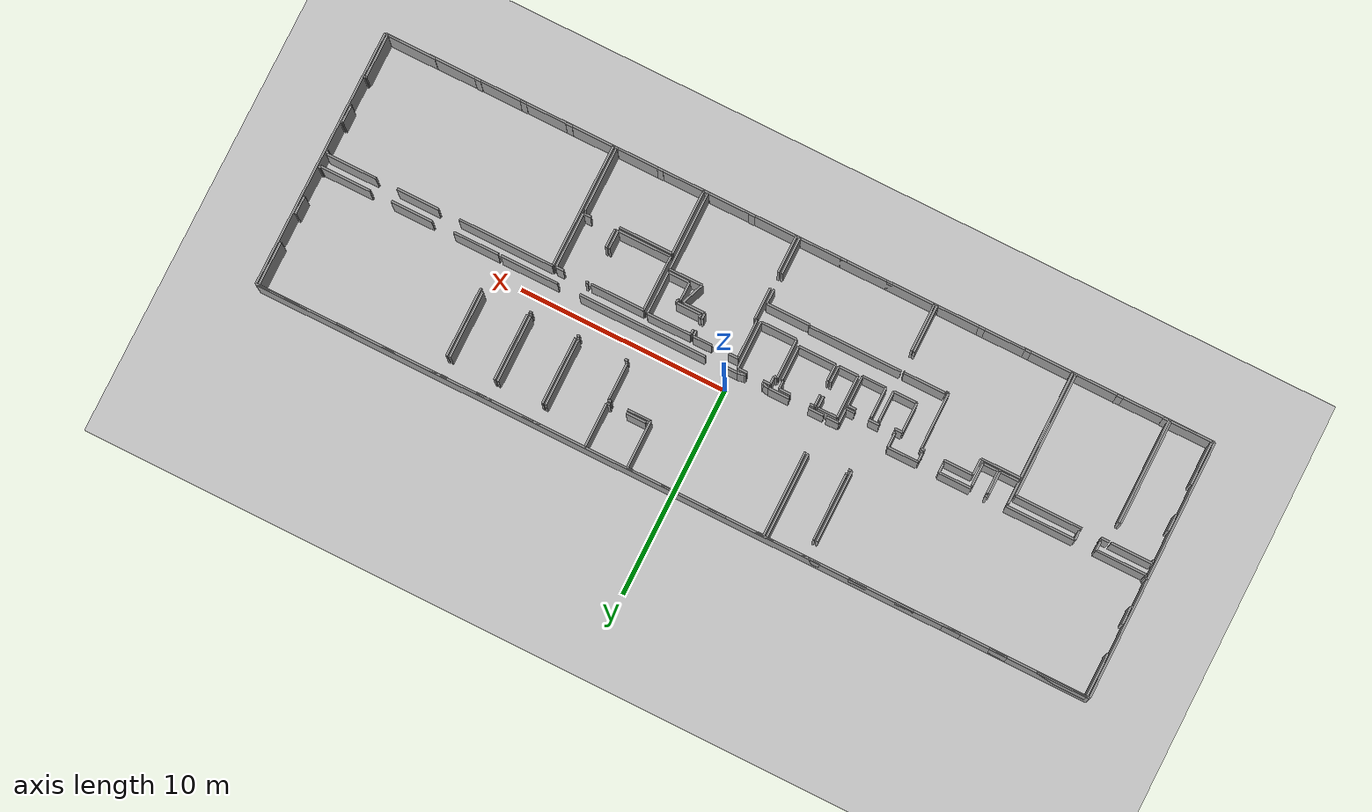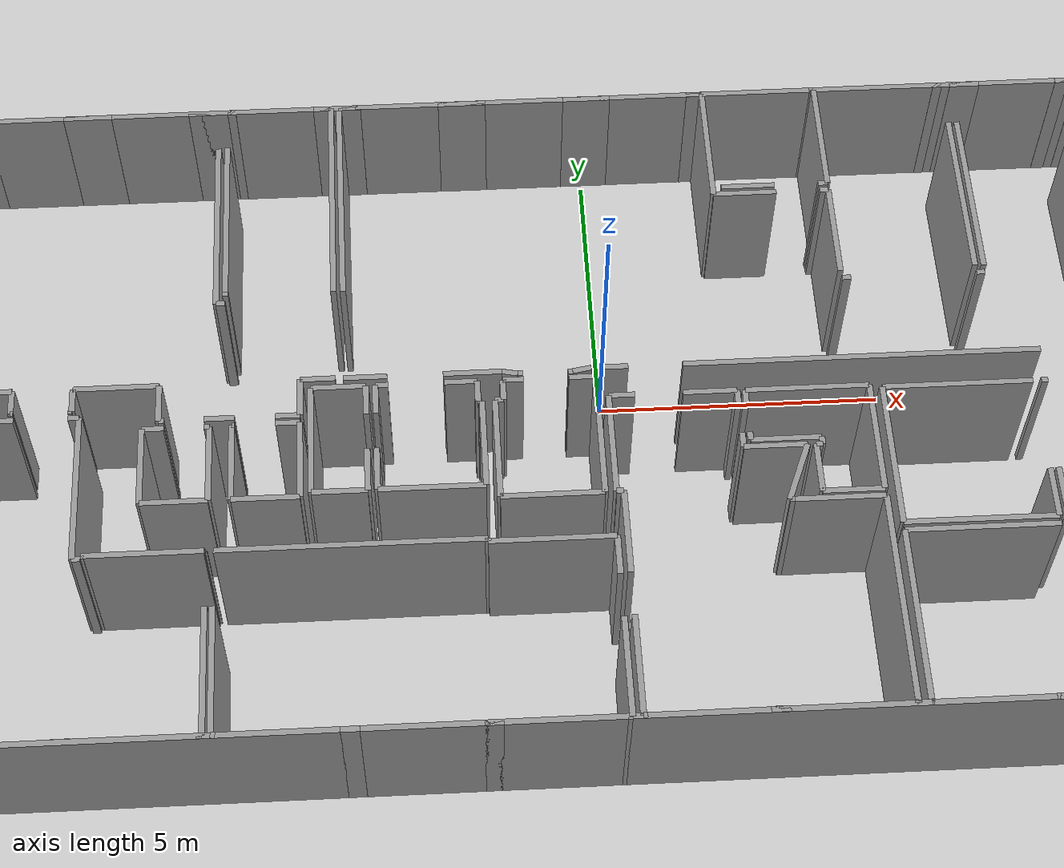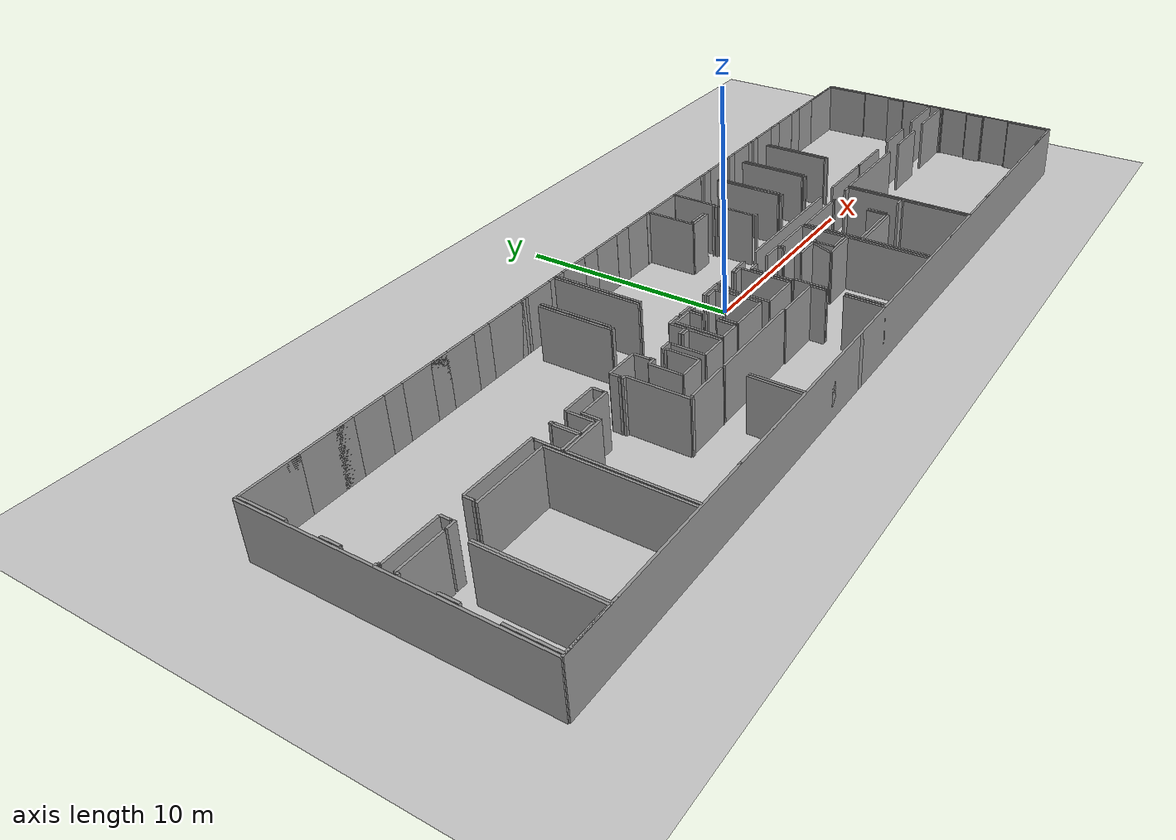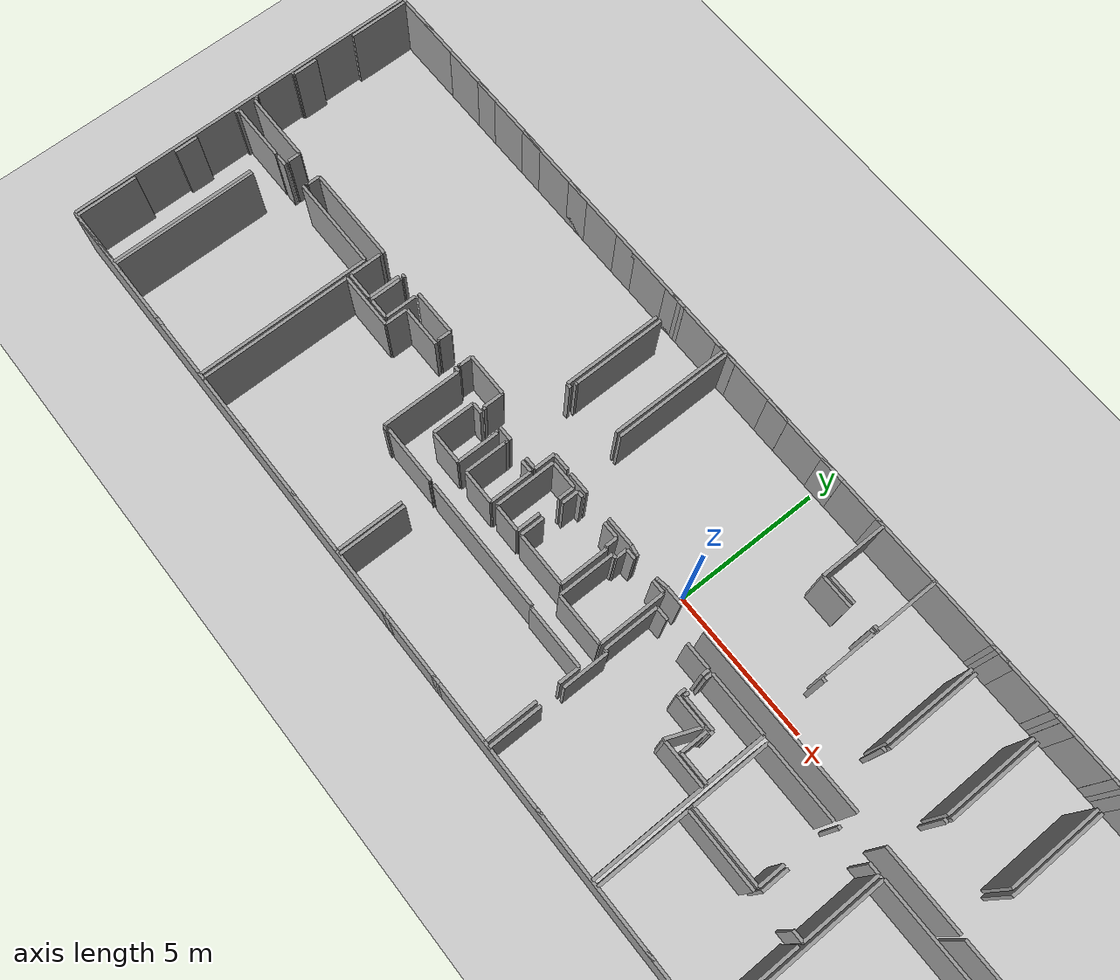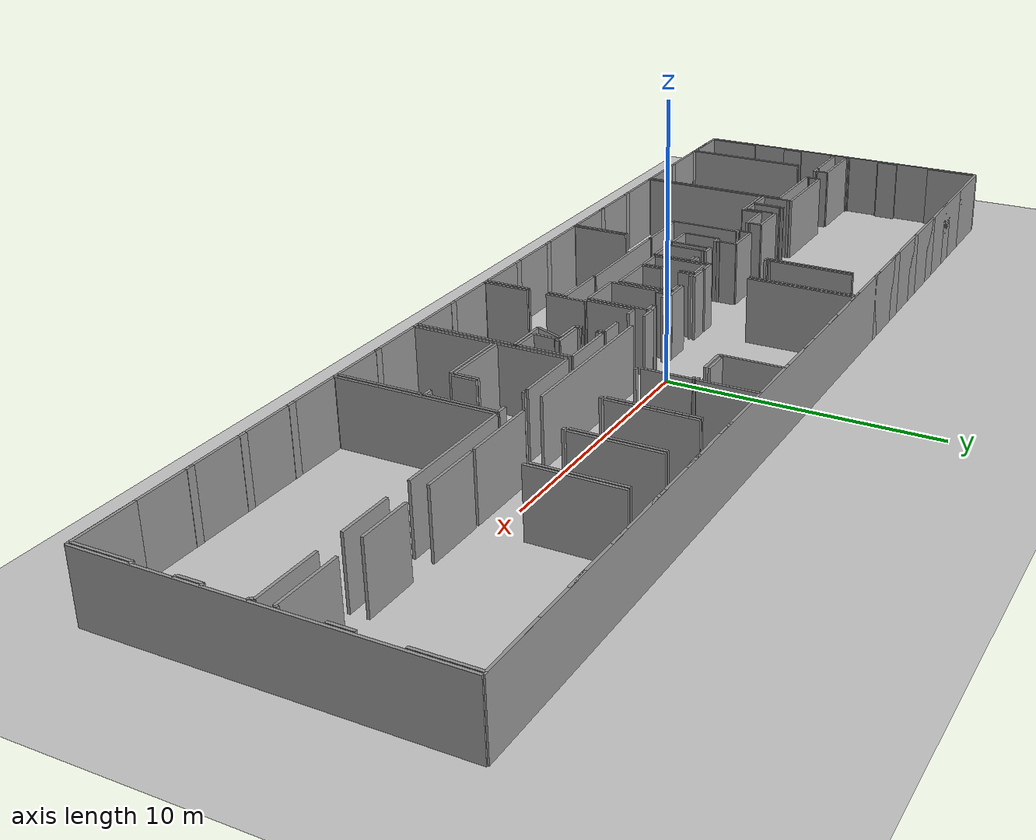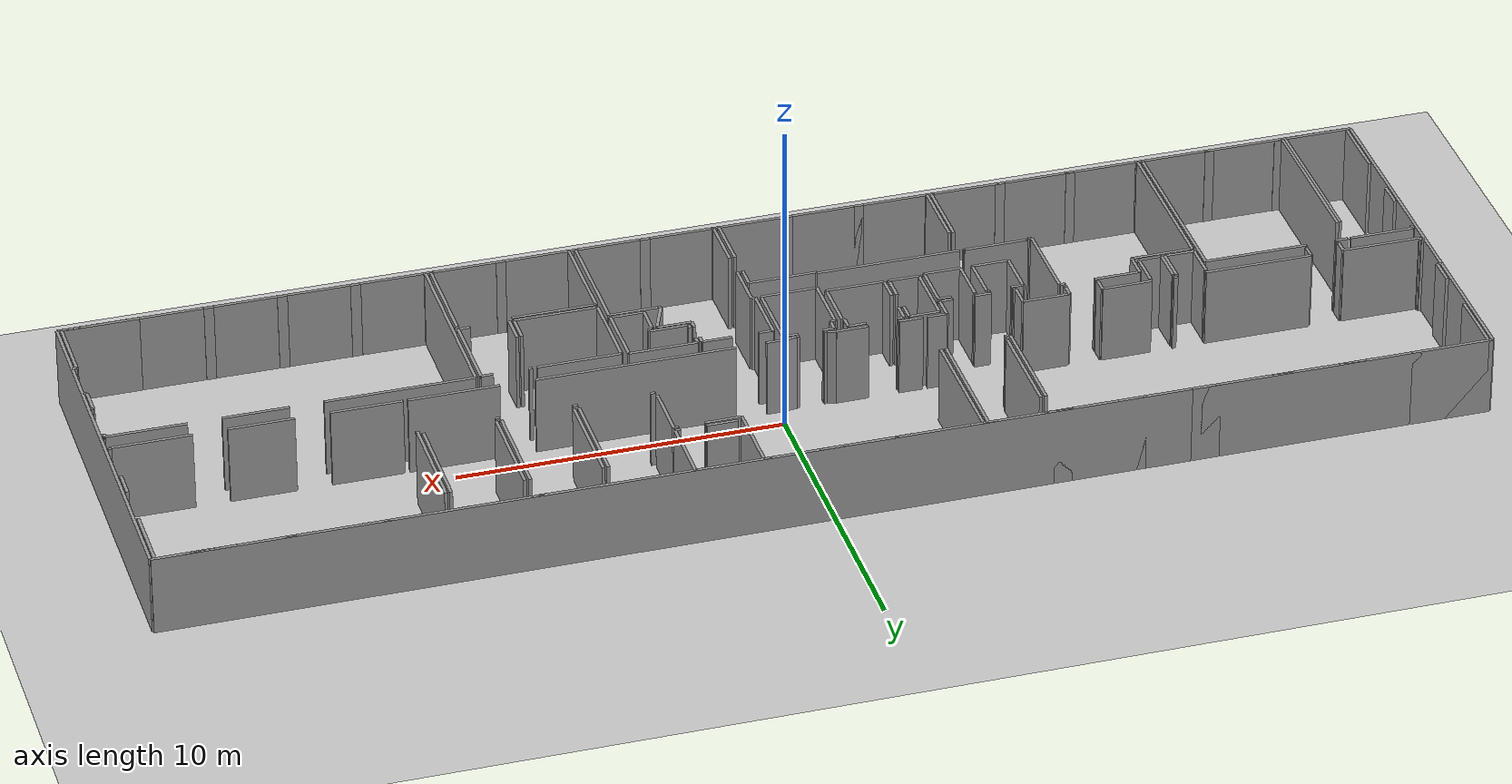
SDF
<sdf version="1.6">
  <world name="default">
    <light name="sun" type="directional">
      <cast_shadows>1</cast_shadows>
      <pose frame="">0 0 10 0 -0 0</pose>
      <diffuse>0.8 0.8 0.8 1</diffuse>
      <specular>0.1 0.1 0.1 1</specular>
      <attenuation>
        <range>1000</range>
        <constant>0.9</constant>
        <linear>0.01</linear>
        <quadratic>0.001</quadratic>
      </attenuation>
      <direction>-0.5 0.5 -1</direction>
    </light>
    <model name="ground_plane">
      <static>1</static>
      <link name="link">
        <collision name="collision">
          <geometry>
            <plane>
              <normal>0 0 1</normal>
              <size>100 100</size>
            </plane>
          </geometry>
          <surface>
            <friction>
              <ode>
                <mu>100</mu>
                <mu2>50</mu2>
              </ode>
              <torsional>
                <ode />
              </torsional>
            </friction>
            <contact>
              <ode />
            </contact>
            <bounce />
          </surface>
          <max_contacts>10</max_contacts>
        </collision>
        <visual name="visual">
          <cast_shadows>0</cast_shadows>
          <geometry>
            <plane>
              <normal>0 0 1</normal>
              <size>100 100</size>
            </plane>
          </geometry>
          <material>
            <script>
              <uri>file://media/materials/scripts/gazebo.material</uri>
              <name>Gazebo/Grey</name>
            </script>
          </material>
        </visual>
        <self_collide>0</self_collide>
        <kinematic>0</kinematic>
        <gravity>1</gravity>
      </link>
    </model>
    <gravity>0 0 -9.8</gravity>
    <magnetic_field>6e-06 2.3e-05 -4.2e-05</magnetic_field>
    <atmosphere type="adiabatic" />
    <physics default="0" name="default_physics" type="ode">
      <max_step_size>0.001</max_step_size>
      <real_time_factor>1</real_time_factor>
      <real_time_update_rate>1000</real_time_update_rate>
    </physics>
    <scene>
      <ambient>0.4 0.4 0.4 1</ambient>
      <background>0.7 0.7 0.7 1</background>
      <shadows>1</shadows>
    </scene>
    <spherical_coordinates>
      <surface_model>EARTH_WGS84</surface_model>
      <latitude_deg>0</latitude_deg>
      <longitude_deg>0</longitude_deg>
      <elevation>0</elevation>
      <heading_deg>0</heading_deg>
    </spherical_coordinates>
  <model name="0510025536_Layout1_PLAN4">
		<static>1</static>
		<link name="Wall_0">
			<collision name="Wall_0_Collision">
				<geometry>
					<box>
						<size>2.08886657941 0.1 2.5</size>
					</box>
				</geometry>
				<pose frame="">1.0444332897 0 1.25 0 0 0</pose>
			</collision>
			<visual name="Wall_0_Visual">
				<pose frame="">1.0444332897 0 1.25 0 0 0</pose>
				<geometry>
					<box>
						<size>2.08886657941 0.1 2.5</size>
					</box>
				</geometry>
				<material>
					<script>
						<uri>file://media/materials/scripts/gazebo.material</uri>
						<name>Gazebo/Grey</name>
					</script>
					<ambient>1 1 1 1</ambient>
				</material>
			</visual>
			<pose frame="">0.12618978028 -12.3596154579 0 0 0 1.57079632679</pose>
		</link>
		<link name="Wall_1">
			<collision name="Wall_1_Collision">
				<geometry>
					<box>
						<size>0.816294112414 0.1 2.5</size>
					</box>
				</geometry>
				<pose frame="">0.408147056207 0 1.25 0 0 0</pose>
			</collision>
			<visual name="Wall_1_Visual">
				<pose frame="">0.408147056207 0 1.25 0 0 0</pose>
				<geometry>
					<box>
						<size>0.816294112414 0.1 2.5</size>
					</box>
				</geometry>
				<material>
					<script>
						<uri>file://media/materials/scripts/gazebo.material</uri>
						<name>Gazebo/Grey</name>
					</script>
					<ambient>1 1 1 1</ambient>
				</material>
			</visual>
			<pose frame="">0.12618978028 -8.83030460917 0 0 0 1.57079632679</pose>
		</link>
		<link name="Wall_2">
			<collision name="Wall_2_Collision">
				<geometry>
					<box>
						<size>0.14887344169 0.1 2.5</size>
					</box>
				</geometry>
				<pose frame="">0.0744367208448 0 1.25 0 0 0</pose>
			</collision>
			<visual name="Wall_2_Visual">
				<pose frame="">0.0744367208448 0 1.25 0 0 0</pose>
				<geometry>
					<box>
						<size>0.14887344169 0.1 2.5</size>
					</box>
				</geometry>
				<material>
					<script>
						<uri>file://media/materials/scripts/gazebo.material</uri>
						<name>Gazebo/Grey</name>
					</script>
					<ambient>1 1 1 1</ambient>
				</material>
			</visual>
			<pose frame="">0.12618978028 -6.59396246076 0 0 0 1.57079632679</pose>
		</link>
		<link name="Wall_3">
			<collision name="Wall_3_Collision">
				<geometry>
					<box>
						<size>1.98275533416 0.1 2.5</size>
					</box>
				</geometry>
				<pose frame="">0.991377667078 0 1.25 0 0 0</pose>
			</collision>
			<visual name="Wall_3_Visual">
				<pose frame="">0.991377667078 0 1.25 0 0 0</pose>
				<geometry>
					<box>
						<size>1.98275533416 0.1 2.5</size>
					</box>
				</geometry>
				<material>
					<script>
						<uri>file://media/materials/scripts/gazebo.material</uri>
						<name>Gazebo/Grey</name>
					</script>
					<ambient>1 1 1 1</ambient>
				</material>
			</visual>
			<pose frame="">0.12618978028 -6.44508901907 0 0 0 0.0</pose>
		</link>
		<link name="Wall_4">
			<collision name="Wall_4_Collision">
				<geometry>
					<box>
						<size>4.96575211905 0.1 2.5</size>
					</box>
				</geometry>
				<pose frame="">2.48287605952 0 1.25 0 0 0</pose>
			</collision>
			<visual name="Wall_4_Visual">
				<pose frame="">2.48287605952 0 1.25 0 0 0</pose>
				<geometry>
					<box>
						<size>4.96575211905 0.1 2.5</size>
					</box>
				</geometry>
				<material>
					<script>
						<uri>file://media/materials/scripts/gazebo.material</uri>
						<name>Gazebo/Grey</name>
					</script>
					<ambient>1 1 1 1</ambient>
				</material>
			</visual>
			<pose frame="">2.10894511443 -7.39113113317 0 0 0 -1.57079632679</pose>
		</link>
		<link name="Wall_5">
			<collision name="Wall_5_Collision">
				<geometry>
					<box>
						<size>1.98275721662 0.1 2.5</size>
					</box>
				</geometry>
				<pose frame="">0.991378608311 0 1.25 0 0 0</pose>
			</collision>
			<visual name="Wall_5_Visual">
				<pose frame="">0.991378608311 0 1.25 0 0 0</pose>
				<geometry>
					<box>
						<size>1.98275721662 0.1 2.5</size>
					</box>
				</geometry>
				<material>
					<script>
						<uri>file://media/materials/scripts/gazebo.material</uri>
						<name>Gazebo/Grey</name>
					</script>
					<ambient>1 1 1 1</ambient>
				</material>
			</visual>
			<pose frame="">2.10894511443 -12.3568832522 0 0 0 -3.14021467016</pose>
		</link>
		<link name="Wall_6">
			<collision name="Wall_6_Collision">
				<geometry>
					<box>
						<size>0.240052865004 0.1 2.5</size>
					</box>
				</geometry>
				<pose frame="">0.120026432502 0 1.25 0 0 0</pose>
			</collision>
			<visual name="Wall_6_Visual">
				<pose frame="">0.120026432502 0 1.25 0 0 0</pose>
				<geometry>
					<box>
						<size>0.240052865004 0.1 2.5</size>
					</box>
				</geometry>
				<material>
					<script>
						<uri>file://media/materials/scripts/gazebo.material</uri>
						<name>Gazebo/Grey</name>
					</script>
					<ambient>1 1 1 1</ambient>
				</material>
			</visual>
			<pose frame="">2.23449949804 -12.3572644902 0 0 0 0.0</pose>
		</link>
		<link name="Wall_7">
			<collision name="Wall_7_Collision">
				<geometry>
					<box>
						<size>0.289041948889 0.1 2.5</size>
					</box>
				</geometry>
				<pose frame="">0.144520974444 0 1.25 0 0 0</pose>
			</collision>
			<visual name="Wall_7_Visual">
				<pose frame="">0.144520974444 0 1.25 0 0 0</pose>
				<geometry>
					<box>
						<size>0.289041948889 0.1 2.5</size>
					</box>
				</geometry>
				<material>
					<script>
						<uri>file://media/materials/scripts/gazebo.material</uri>
						<name>Gazebo/Grey</name>
					</script>
					<ambient>1 1 1 1</ambient>
				</material>
			</visual>
			<pose frame="">4.41384656441 -12.3572644902 0 0 0 0.0</pose>
		</link>
		<link name="Wall_8">
			<collision name="Wall_8_Collision">
				<geometry>
					<box>
						<size>0.0716727452949 0.1 2.5</size>
					</box>
				</geometry>
				<pose frame="">0.0358363726474 0 1.25 0 0 0</pose>
			</collision>
			<visual name="Wall_8_Visual">
				<pose frame="">0.0358363726474 0 1.25 0 0 0</pose>
				<geometry>
					<box>
						<size>0.0716727452949 0.1 2.5</size>
					</box>
				</geometry>
				<material>
					<script>
						<uri>file://media/materials/scripts/gazebo.material</uri>
						<name>Gazebo/Grey</name>
					</script>
					<ambient>1 1 1 1</ambient>
				</material>
			</visual>
			<pose frame="">6.63290592317 -12.3572644902 0 0 0 0.0</pose>
		</link>
		<link name="Wall_9">
			<collision name="Wall_9_Collision">
				<geometry>
					<box>
						<size>5.91211193148 0.1 2.5</size>
					</box>
				</geometry>
				<pose frame="">2.95605596574 0 1.25 0 0 0</pose>
			</collision>
			<visual name="Wall_9_Visual">
				<pose frame="">2.95605596574 0 1.25 0 0 0</pose>
				<geometry>
					<box>
						<size>5.91211193148 0.1 2.5</size>
					</box>
				</geometry>
				<material>
					<script>
						<uri>file://media/materials/scripts/gazebo.material</uri>
						<name>Gazebo/Grey</name>
					</script>
					<ambient>1 1 1 1</ambient>
				</material>
			</visual>
			<pose frame="">6.70457866846 -12.3572644902 0 0 0 1.57079632679</pose>
		</link>
		<link name="Wall_10">
			<collision name="Wall_10_Collision">
				<geometry>
					<box>
						<size>3.19356724403 0.1 2.5</size>
					</box>
				</geometry>
				<pose frame="">1.59678362202 0 1.25 0 0 0</pose>
			</collision>
			<visual name="Wall_10_Visual">
				<pose frame="">1.59678362202 0 1.25 0 0 0</pose>
				<geometry>
					<box>
						<size>3.19356724403 0.1 2.5</size>
					</box>
				</geometry>
				<material>
					<script>
						<uri>file://media/materials/scripts/gazebo.material</uri>
						<name>Gazebo/Grey</name>
					</script>
					<ambient>1 1 1 1</ambient>
				</material>
			</visual>
			<pose frame="">6.70457866846 -6.44515255874 0 0 0 3.14159265359</pose>
		</link>
		<link name="Wall_11">
			<collision name="Wall_11_Collision">
				<geometry>
					<box>
						<size>0.405637239329 0.1 2.5</size>
					</box>
				</geometry>
				<pose frame="">0.202818619664 0 1.25 0 0 0</pose>
			</collision>
			<visual name="Wall_11_Visual">
				<pose frame="">0.202818619664 0 1.25 0 0 0</pose>
				<geometry>
					<box>
						<size>0.405637239329 0.1 2.5</size>
					</box>
				</geometry>
				<material>
					<script>
						<uri>file://media/materials/scripts/gazebo.material</uri>
						<name>Gazebo/Grey</name>
					</script>
					<ambient>1 1 1 1</ambient>
				</material>
			</visual>
			<pose frame="">2.60233063502 -6.44515255874 0 0 0 3.14159265359</pose>
		</link>
		<link name="Wall_12">
			<collision name="Wall_12_Collision">
				<geometry>
					<box>
						<size>4.97426643454 0.1 2.5</size>
					</box>
				</geometry>
				<pose frame="">2.48713321727 0 1.25 0 0 0</pose>
			</collision>
			<visual name="Wall_12_Visual">
				<pose frame="">2.48713321727 0 1.25 0 0 0</pose>
				<geometry>
					<box>
						<size>4.97426643454 0.1 2.5</size>
					</box>
				</geometry>
				<material>
					<script>
						<uri>file://media/materials/scripts/gazebo.material</uri>
						<name>Gazebo/Grey</name>
					</script>
					<ambient>1 1 1 1</ambient>
				</material>
			</visual>
			<pose frame="">2.19669339569 -7.38433238871 0 0 0 -1.57079632679</pose>
		</link>
		<link name="Wall_13">
			<collision name="Wall_13_Collision">
				<geometry>
					<box>
						<size>0.0378296420746 0.1 2.5</size>
					</box>
				</geometry>
				<pose frame="">0.0189148210373 0 1.25 0 0 0</pose>
			</collision>
			<visual name="Wall_13_Visual">
				<pose frame="">0.0189148210373 0 1.25 0 0 0</pose>
				<geometry>
					<box>
						<size>0.0378296420746 0.1 2.5</size>
					</box>
				</geometry>
				<material>
					<script>
						<uri>file://media/materials/scripts/gazebo.material</uri>
						<name>Gazebo/Grey</name>
					</script>
					<ambient>1 1 1 1</ambient>
				</material>
			</visual>
			<pose frame="">2.19669339569 -12.3585988232 0 0 0 0.0352794735935</pose>
		</link>
		<link name="Wall_14">
			<collision name="Wall_14_Collision">
				<geometry>
					<box>
						<size>1.09078547737 0.1 2.5</size>
					</box>
				</geometry>
				<pose frame="">0.545392738687 0 1.25 0 0 0</pose>
			</collision>
			<visual name="Wall_14_Visual">
				<pose frame="">0.545392738687 0 1.25 0 0 0</pose>
				<geometry>
					<box>
						<size>1.09078547737 0.1 2.5</size>
					</box>
				</geometry>
				<material>
					<script>
						<uri>file://media/materials/scripts/gazebo.material</uri>
						<name>Gazebo/Grey</name>
					</script>
					<ambient>1 1 1 1</ambient>
				</material>
			</visual>
			<pose frame="">6.84411177898 -7.07946906254 0 0 0 1.57079632679</pose>
		</link>
		<link name="Wall_15">
			<collision name="Wall_15_Collision">
				<geometry>
					<box>
						<size>0.0507046549161 0.1 2.5</size>
					</box>
				</geometry>
				<pose frame="">0.025352327458 0 1.25 0 0 0</pose>
			</collision>
			<visual name="Wall_15_Visual">
				<pose frame="">0.025352327458 0 1.25 0 0 0</pose>
				<geometry>
					<box>
						<size>0.0507046549161 0.1 2.5</size>
					</box>
				</geometry>
				<material>
					<script>
						<uri>file://media/materials/scripts/gazebo.material</uri>
						<name>Gazebo/Grey</name>
					</script>
					<ambient>1 1 1 1</ambient>
				</material>
			</visual>
			<pose frame="">6.84411177898 -5.98868358516 0 0 0 0.0</pose>
		</link>
		<link name="Wall_16">
			<collision name="Wall_16_Collision">
				<geometry>
					<box>
						<size>1.08868866834 0.1 2.5</size>
					</box>
				</geometry>
				<pose frame="">0.544344334168 0 1.25 0 0 0</pose>
			</collision>
			<visual name="Wall_16_Visual">
				<pose frame="">0.544344334168 0 1.25 0 0 0</pose>
				<geometry>
					<box>
						<size>1.08868866834 0.1 2.5</size>
					</box>
				</geometry>
				<material>
					<script>
						<uri>file://media/materials/scripts/gazebo.material</uri>
						<name>Gazebo/Grey</name>
					</script>
					<ambient>1 1 1 1</ambient>
				</material>
			</visual>
			<pose frame="">7.76912226303 -5.98868358516 0 0 0 -1.57079632679</pose>
		</link>
		<link name="Wall_17">
			<collision name="Wall_17_Collision">
				<geometry>
					<box>
						<size>0.92501286056 0.1 2.5</size>
					</box>
				</geometry>
				<pose frame="">0.46250643028 0 1.25 0 0 0</pose>
			</collision>
			<visual name="Wall_17_Visual">
				<pose frame="">0.46250643028 0 1.25 0 0 0</pose>
				<geometry>
					<box>
						<size>0.92501286056 0.1 2.5</size>
					</box>
				</geometry>
				<material>
					<script>
						<uri>file://media/materials/scripts/gazebo.material</uri>
						<name>Gazebo/Grey</name>
					</script>
					<ambient>1 1 1 1</ambient>
				</material>
			</visual>
			<pose frame="">7.76912226303 -7.0773722535 0 0 0 -3.13932586258</pose>
		</link>
		<link name="Wall_18">
			<collision name="Wall_18_Collision">
				<geometry>
					<box>
						<size>1.088752208 0.1 2.5</size>
					</box>
				</geometry>
				<pose frame="">0.544376104002 0 1.25 0 0 0</pose>
			</collision>
			<visual name="Wall_18_Visual">
				<pose frame="">0.544376104002 0 1.25 0 0 0</pose>
				<geometry>
					<box>
						<size>1.088752208 0.1 2.5</size>
					</box>
				</geometry>
				<material>
					<script>
						<uri>file://media/materials/scripts/gazebo.material</uri>
						<name>Gazebo/Grey</name>
					</script>
					<ambient>1 1 1 1</ambient>
				</material>
			</visual>
			<pose frame="">7.86894308117 -7.07997737988 0 0 0 1.57079632679</pose>
		</link>
		<link name="Wall_19">
			<collision name="Wall_19_Collision">
				<geometry>
					<box>
						<size>0.0371071660037 0.1 2.5</size>
					</box>
				</geometry>
				<pose frame="">0.0185535830019 0 1.25 0 0 0</pose>
			</collision>
			<visual name="Wall_19_Visual">
				<pose frame="">0.0185535830019 0 1.25 0 0 0</pose>
				<geometry>
					<box>
						<size>0.0371071660037 0.1 2.5</size>
					</box>
				</geometry>
				<material>
					<script>
						<uri>file://media/materials/scripts/gazebo.material</uri>
						<name>Gazebo/Grey</name>
					</script>
					<ambient>1 1 1 1</ambient>
				</material>
			</visual>
			<pose frame="">7.86894308117 -5.99122517187 0 0 0 0.0</pose>
		</link>
		<link name="Wall_20">
			<collision name="Wall_20_Collision">
				<geometry>
					<box>
						<size>1.07985665451 0.1 2.5</size>
					</box>
				</geometry>
				<pose frame="">0.539928327255 0 1.25 0 0 0</pose>
			</collision>
			<visual name="Wall_20_Visual">
				<pose frame="">0.539928327255 0 1.25 0 0 0</pose>
				<geometry>
					<box>
						<size>1.07985665451 0.1 2.5</size>
					</box>
				</geometry>
				<material>
					<script>
						<uri>file://media/materials/scripts/gazebo.material</uri>
						<name>Gazebo/Grey</name>
					</script>
					<ambient>1 1 1 1</ambient>
				</material>
			</visual>
			<pose frame="">8.59037246953 -5.99122517187 0 0 0 -1.57079632679</pose>
		</link>
		<link name="Wall_21">
			<collision name="Wall_21_Collision">
				<geometry>
					<box>
						<size>0.721484229399 0.1 2.5</size>
					</box>
				</geometry>
				<pose frame="">0.3607421147 0 1.25 0 0 0</pose>
			</collision>
			<visual name="Wall_21_Visual">
				<pose frame="">0.3607421147 0 1.25 0 0 0</pose>
				<geometry>
					<box>
						<size>0.721484229399 0.1 2.5</size>
					</box>
				</geometry>
				<material>
					<script>
						<uri>file://media/materials/scripts/gazebo.material</uri>
						<name>Gazebo/Grey</name>
					</script>
					<ambient>1 1 1 1</ambient>
				</material>
			</visual>
			<pose frame="">8.59037246953 -7.07108182638 0 0 0 -3.12926282221</pose>
		</link>
		<link name="Wall_22">
			<collision name="Wall_22_Collision">
				<geometry>
					<box>
						<size>5.14398088727 0.1 2.5</size>
					</box>
				</geometry>
				<pose frame="">2.57199044363 0 1.25 0 0 0</pose>
			</collision>
			<visual name="Wall_22_Visual">
				<pose frame="">2.57199044363 0 1.25 0 0 0</pose>
				<geometry>
					<box>
						<size>5.14398088727 0.1 2.5</size>
					</box>
				</geometry>
				<material>
					<script>
						<uri>file://media/materials/scripts/gazebo.material</uri>
						<name>Gazebo/Grey</name>
					</script>
					<ambient>1 1 1 1</ambient>
				</material>
			</visual>
			<pose frame="">6.85478644318 -12.3631101397 0 0 0 1.57079632679</pose>
		</link>
		<link name="Wall_23">
			<collision name="Wall_23_Collision">
				<geometry>
					<box>
						<size>1.91203568388 0.1 2.5</size>
					</box>
				</geometry>
				<pose frame="">0.956017841939 0 1.25 0 0 0</pose>
			</collision>
			<visual name="Wall_23_Visual">
				<pose frame="">0.956017841939 0 1.25 0 0 0</pose>
				<geometry>
					<box>
						<size>1.91203568388 0.1 2.5</size>
					</box>
				</geometry>
				<material>
					<script>
						<uri>file://media/materials/scripts/gazebo.material</uri>
						<name>Gazebo/Grey</name>
					</script>
					<ambient>1 1 1 1</ambient>
				</material>
			</visual>
			<pose frame="">6.85478644318 -7.21912925239 0 0 0 0.0</pose>
		</link>
		<link name="Wall_24">
			<collision name="Wall_24_Collision">
				<geometry>
					<box>
						<size>0.774993328335 0.1 2.5</size>
					</box>
				</geometry>
				<pose frame="">0.387496664167 0 1.25 0 0 0</pose>
			</collision>
			<visual name="Wall_24_Visual">
				<pose frame="">0.387496664167 0 1.25 0 0 0</pose>
				<geometry>
					<box>
						<size>0.774993328335 0.1 2.5</size>
					</box>
				</geometry>
				<material>
					<script>
						<uri>file://media/materials/scripts/gazebo.material</uri>
						<name>Gazebo/Grey</name>
					</script>
					<ambient>1 1 1 1</ambient>
				</material>
			</visual>
			<pose frame="">8.76682212705 -7.21912925239 0 0 0 1.57079632679</pose>
		</link>
		<link name="Wall_25">
			<collision name="Wall_25_Collision">
				<geometry>
					<box>
						<size>1.41445654522 0.1 2.5</size>
					</box>
				</geometry>
				<pose frame="">0.707228272611 0 1.25 0 0 0</pose>
			</collision>
			<visual name="Wall_25_Visual">
				<pose frame="">0.707228272611 0 1.25 0 0 0</pose>
				<geometry>
					<box>
						<size>1.41445654522 0.1 2.5</size>
					</box>
				</geometry>
				<material>
					<script>
						<uri>file://media/materials/scripts/gazebo.material</uri>
						<name>Gazebo/Grey</name>
					</script>
					<ambient>1 1 1 1</ambient>
				</material>
			</visual>
			<pose frame="">8.76682212705 -6.44413592406 0 0 0 0.0</pose>
		</link>
		<link name="Wall_26">
			<collision name="Wall_26_Collision">
				<geometry>
					<box>
						<size>0.180516196261 0.1 2.5</size>
					</box>
				</geometry>
				<pose frame="">0.0902580981307 0 1.25 0 0 0</pose>
			</collision>
			<visual name="Wall_26_Visual">
				<pose frame="">0.0902580981307 0 1.25 0 0 0</pose>
				<geometry>
					<box>
						<size>0.180516196261 0.1 2.5</size>
					</box>
				</geometry>
				<material>
					<script>
						<uri>file://media/materials/scripts/gazebo.material</uri>
						<name>Gazebo/Grey</name>
					</script>
					<ambient>1 1 1 1</ambient>
				</material>
			</visual>
			<pose frame="">11.0957415715 -6.44413592406 0 0 0 0.0</pose>
		</link>
		<link name="Wall_27">
			<collision name="Wall_27_Collision">
				<geometry>
					<box>
						<size>2.70348578618 0.1 2.5</size>
					</box>
				</geometry>
				<pose frame="">1.35174289309 0 1.25 0 0 0</pose>
			</collision>
			<visual name="Wall_27_Visual">
				<pose frame="">1.35174289309 0 1.25 0 0 0</pose>
				<geometry>
					<box>
						<size>2.70348578618 0.1 2.5</size>
					</box>
				</geometry>
				<material>
					<script>
						<uri>file://media/materials/scripts/gazebo.material</uri>
						<name>Gazebo/Grey</name>
					</script>
					<ambient>1 1 1 1</ambient>
				</material>
			</visual>
			<pose frame="">11.2762577677 -6.44413592406 0 0 0 -1.57079632679</pose>
		</link>
		<link name="Wall_28">
			<collision name="Wall_28_Collision">
				<geometry>
					<box>
						<size>0.140930983213 0.1 2.5</size>
					</box>
				</geometry>
				<pose frame="">0.0704654916064 0 1.25 0 0 0</pose>
			</collision>
			<visual name="Wall_28_Visual">
				<pose frame="">0.0704654916064 0 1.25 0 0 0</pose>
				<geometry>
					<box>
						<size>0.140930983213 0.1 2.5</size>
					</box>
				</geometry>
				<material>
					<script>
						<uri>file://media/materials/scripts/gazebo.material</uri>
						<name>Gazebo/Grey</name>
					</script>
					<ambient>1 1 1 1</ambient>
				</material>
			</visual>
			<pose frame="">11.2762577677 -9.14762171023 0 0 0 0.0</pose>
		</link>
		<link name="Wall_29">
			<collision name="Wall_29_Collision">
				<geometry>
					<box>
						<size>0.0515942102655 0.1 2.5</size>
					</box>
				</geometry>
				<pose frame="">0.0257971051327 0 1.25 0 0 0</pose>
			</collision>
			<visual name="Wall_29_Visual">
				<pose frame="">0.0257971051327 0 1.25 0 0 0</pose>
				<geometry>
					<box>
						<size>0.0515942102655 0.1 2.5</size>
					</box>
				</geometry>
				<material>
					<script>
						<uri>file://media/materials/scripts/gazebo.material</uri>
						<name>Gazebo/Grey</name>
					</script>
					<ambient>1 1 1 1</ambient>
				</material>
			</visual>
			<pose frame="">11.4171887509 -9.14762171023 0 0 0 1.57079632679</pose>
		</link>
		<link name="Wall_30">
			<collision name="Wall_30_Collision">
				<geometry>
					<box>
						<size>1.99203212566 0.1 2.5</size>
					</box>
				</geometry>
				<pose frame="">0.996016062828 0 1.25 0 0 0</pose>
			</collision>
			<visual name="Wall_30_Visual">
				<pose frame="">0.996016062828 0 1.25 0 0 0</pose>
				<geometry>
					<box>
						<size>1.99203212566 0.1 2.5</size>
					</box>
				</geometry>
				<material>
					<script>
						<uri>file://media/materials/scripts/gazebo.material</uri>
						<name>Gazebo/Grey</name>
					</script>
					<ambient>1 1 1 1</ambient>
				</material>
			</visual>
			<pose frame="">11.4171887509 -9.09602749997 0 0 0 0.0</pose>
		</link>
		<link name="Wall_31">
			<collision name="Wall_31_Collision">
				<geometry>
					<box>
						<size>0.0273220571603 0.1 2.5</size>
					</box>
				</geometry>
				<pose frame="">0.0136610285801 0 1.25 0 0 0</pose>
			</collision>
			<visual name="Wall_31_Visual">
				<pose frame="">0.0136610285801 0 1.25 0 0 0</pose>
				<geometry>
					<box>
						<size>0.0273220571603 0.1 2.5</size>
					</box>
				</geometry>
				<material>
					<script>
						<uri>file://media/materials/scripts/gazebo.material</uri>
						<name>Gazebo/Grey</name>
					</script>
					<ambient>1 1 1 1</ambient>
				</material>
			</visual>
			<pose frame="">13.4092208766 -9.09602749997 0 0 0 -1.57079632679</pose>
		</link>
		<link name="Wall_32">
			<collision name="Wall_32_Collision">
				<geometry>
					<box>
						<size>0.0153765996111 0.1 2.5</size>
					</box>
				</geometry>
				<pose frame="">0.00768829980557 0 1.25 0 0 0</pose>
			</collision>
			<visual name="Wall_32_Visual">
				<pose frame="">0.00768829980557 0 1.25 0 0 0</pose>
				<geometry>
					<box>
						<size>0.0153765996111 0.1 2.5</size>
					</box>
				</geometry>
				<material>
					<script>
						<uri>file://media/materials/scripts/gazebo.material</uri>
						<name>Gazebo/Grey</name>
					</script>
					<ambient>1 1 1 1</ambient>
				</material>
			</visual>
			<pose frame="">13.4092208766 -9.12334955713 0 0 0 0.0</pose>
		</link>
		<link name="Wall_33">
			<collision name="Wall_33_Collision">
				<geometry>
					<box>
						<size>2.25146458934 0.1 2.5</size>
					</box>
				</geometry>
				<pose frame="">1.12573229467 0 1.25 0 0 0</pose>
			</collision>
			<visual name="Wall_33_Visual">
				<pose frame="">1.12573229467 0 1.25 0 0 0</pose>
				<geometry>
					<box>
						<size>2.25146458934 0.1 2.5</size>
					</box>
				</geometry>
				<material>
					<script>
						<uri>file://media/materials/scripts/gazebo.material</uri>
						<name>Gazebo/Grey</name>
					</script>
					<ambient>1 1 1 1</ambient>
				</material>
			</visual>
			<pose frame="">13.4245974762 -10.112471566 0 0 0 -1.57079632679</pose>
		</link>
		<link name="Wall_34">
			<collision name="Wall_34_Collision">
				<geometry>
					<box>
						<size>0.0913700423174 0.1 2.5</size>
					</box>
				</geometry>
				<pose frame="">0.0456850211587 0 1.25 0 0 0</pose>
			</collision>
			<visual name="Wall_34_Visual">
				<pose frame="">0.0456850211587 0 1.25 0 0 0</pose>
				<geometry>
					<box>
						<size>0.0913700423174 0.1 2.5</size>
					</box>
				</geometry>
				<material>
					<script>
						<uri>file://media/materials/scripts/gazebo.material</uri>
						<name>Gazebo/Grey</name>
					</script>
					<ambient>1 1 1 1</ambient>
				</material>
			</visual>
			<pose frame="">13.4245974762 -12.3639361553 0 0 0 3.14159265359</pose>
		</link>
		<link name="Wall_35">
			<collision name="Wall_35_Collision">
				<geometry>
					<box>
						<size>0.298636438729 0.1 2.5</size>
					</box>
				</geometry>
				<pose frame="">0.149318219364 0 1.25 0 0 0</pose>
			</collision>
			<visual name="Wall_35_Visual">
				<pose frame="">0.149318219364 0 1.25 0 0 0</pose>
				<geometry>
					<box>
						<size>0.298636438729 0.1 2.5</size>
					</box>
				</geometry>
				<material>
					<script>
						<uri>file://media/materials/scripts/gazebo.material</uri>
						<name>Gazebo/Grey</name>
					</script>
					<ambient>1 1 1 1</ambient>
				</material>
			</visual>
			<pose frame="">11.4007955166 -12.3639361553 0 0 0 3.14159265359</pose>
		</link>
		<link name="Wall_36">
			<collision name="Wall_36_Collision">
				<geometry>
					<box>
						<size>0.293743884307 0.1 2.5</size>
					</box>
				</geometry>
				<pose frame="">0.146871942153 0 1.25 0 0 0</pose>
			</collision>
			<visual name="Wall_36_Visual">
				<pose frame="">0.146871942153 0 1.25 0 0 0</pose>
				<geometry>
					<box>
						<size>0.293743884307 0.1 2.5</size>
					</box>
				</geometry>
				<material>
					<script>
						<uri>file://media/materials/scripts/gazebo.material</uri>
						<name>Gazebo/Grey</name>
					</script>
					<ambient>1 1 1 1</ambient>
				</material>
			</visual>
			<pose frame="">9.16273779721 -12.3639361553 0 0 0 3.14159265359</pose>
		</link>
		<link name="Wall_37">
			<collision name="Wall_37_Collision">
				<geometry>
					<box>
						<size>0.0819703334697 0.1 2.5</size>
					</box>
				</geometry>
				<pose frame="">0.0409851667349 0 1.25 0 0 0</pose>
			</collision>
			<visual name="Wall_37_Visual">
				<pose frame="">0.0409851667349 0 1.25 0 0 0</pose>
				<geometry>
					<box>
						<size>0.0819703334697 0.1 2.5</size>
					</box>
				</geometry>
				<material>
					<script>
						<uri>file://media/materials/scripts/gazebo.material</uri>
						<name>Gazebo/Grey</name>
					</script>
					<ambient>1 1 1 1</ambient>
				</material>
			</visual>
			<pose frame="">6.93675261466 -12.3639361553 0 0 0 3.13151547533</pose>
		</link>
		<link name="Wall_38">
			<collision name="Wall_38_Collision">
				<geometry>
					<box>
						<size>1.4261478441 0.1 2.5</size>
					</box>
				</geometry>
				<pose frame="">0.71307392205 0 1.25 0 0 0</pose>
			</collision>
			<visual name="Wall_38_Visual">
				<pose frame="">0.71307392205 0 1.25 0 0 0</pose>
				<geometry>
					<box>
						<size>1.4261478441 0.1 2.5</size>
					</box>
				</geometry>
				<material>
					<script>
						<uri>file://media/materials/scripts/gazebo.material</uri>
						<name>Gazebo/Grey</name>
					</script>
					<ambient>1 1 1 1</ambient>
				</material>
			</visual>
			<pose frame="">12.3259966197 -8.15316236927 0 0 0 1.57079632679</pose>
		</link>
		<link name="Wall_39">
			<collision name="Wall_39_Collision">
				<geometry>
					<box>
						<size>0.367640517975 0.1 2.5</size>
					</box>
				</geometry>
				<pose frame="">0.183820258988 0 1.25 0 0 0</pose>
			</collision>
			<visual name="Wall_39_Visual">
				<pose frame="">0.183820258988 0 1.25 0 0 0</pose>
				<geometry>
					<box>
						<size>0.367640517975 0.1 2.5</size>
					</box>
				</geometry>
				<material>
					<script>
						<uri>file://media/materials/scripts/gazebo.material</uri>
						<name>Gazebo/Grey</name>
					</script>
					<ambient>1 1 1 1</ambient>
				</material>
			</visual>
			<pose frame="">12.3259966197 -6.72701452517 0 0 0 0.0</pose>
		</link>
		<link name="Wall_40">
			<collision name="Wall_40_Collision">
				<geometry>
					<box>
						<size>0.0855243928785 0.1 2.5</size>
					</box>
				</geometry>
				<pose frame="">0.0427621964392 0 1.25 0 0 0</pose>
			</collision>
			<visual name="Wall_40_Visual">
				<pose frame="">0.0427621964392 0 1.25 0 0 0</pose>
				<geometry>
					<box>
						<size>0.0855243928785 0.1 2.5</size>
					</box>
				</geometry>
				<material>
					<script>
						<uri>file://media/materials/scripts/gazebo.material</uri>
						<name>Gazebo/Grey</name>
					</script>
					<ambient>1 1 1 1</ambient>
				</material>
			</visual>
			<pose frame="">13.3676023942 -6.72701452517 0 0 0 0.0</pose>
		</link>
		<link name="Wall_41">
			<collision name="Wall_41_Collision">
				<geometry>
					<box>
						<size>1.42494059041 0.1 2.5</size>
					</box>
				</geometry>
				<pose frame="">0.712470295205 0 1.25 0 0 0</pose>
			</collision>
			<visual name="Wall_41_Visual">
				<pose frame="">0.712470295205 0 1.25 0 0 0</pose>
				<geometry>
					<box>
						<size>1.42494059041 0.1 2.5</size>
					</box>
				</geometry>
				<material>
					<script>
						<uri>file://media/materials/scripts/gazebo.material</uri>
						<name>Gazebo/Grey</name>
					</script>
					<ambient>1 1 1 1</ambient>
				</material>
			</visual>
			<pose frame="">13.4531267871 -6.72701452517 0 0 0 -1.57079632679</pose>
		</link>
		<link name="Wall_42">
			<collision name="Wall_42_Collision">
				<geometry>
					<box>
						<size>1.1271308139 0.1 2.5</size>
					</box>
				</geometry>
				<pose frame="">0.56356540695 0 1.25 0 0 0</pose>
			</collision>
			<visual name="Wall_42_Visual">
				<pose frame="">0.56356540695 0 1.25 0 0 0</pose>
				<geometry>
					<box>
						<size>1.1271308139 0.1 2.5</size>
					</box>
				</geometry>
				<material>
					<script>
						<uri>file://media/materials/scripts/gazebo.material</uri>
						<name>Gazebo/Grey</name>
					</script>
					<ambient>1 1 1 1</ambient>
				</material>
			</visual>
			<pose frame="">13.4531267871 -8.15195511558 0 0 0 -3.14052156769</pose>
		</link>
		<link name="Wall_43">
			<collision name="Wall_43_Collision">
				<geometry>
					<box>
						<size>1.43822038098 0.1 2.5</size>
					</box>
				</geometry>
				<pose frame="">0.719110190492 0 1.25 0 0 0</pose>
			</collision>
			<visual name="Wall_43_Visual">
				<pose frame="">0.719110190492 0 1.25 0 0 0</pose>
				<geometry>
					<box>
						<size>1.43822038098 0.1 2.5</size>
					</box>
				</geometry>
				<material>
					<script>
						<uri>file://media/materials/scripts/gazebo.material</uri>
						<name>Gazebo/Grey</name>
					</script>
					<ambient>1 1 1 1</ambient>
				</material>
			</visual>
			<pose frame="">13.8250244628 -8.15341652794 0 0 0 1.57079632679</pose>
		</link>
		<link name="Wall_44">
			<collision name="Wall_44_Collision">
				<geometry>
					<box>
						<size>0.0514671309298 0.1 2.5</size>
					</box>
				</geometry>
				<pose frame="">0.0257335654649 0 1.25 0 0 0</pose>
			</collision>
			<visual name="Wall_44_Visual">
				<pose frame="">0.0257335654649 0 1.25 0 0 0</pose>
				<geometry>
					<box>
						<size>0.0514671309298 0.1 2.5</size>
					</box>
				</geometry>
				<material>
					<script>
						<uri>file://media/materials/scripts/gazebo.material</uri>
						<name>Gazebo/Grey</name>
					</script>
					<ambient>1 1 1 1</ambient>
				</material>
			</visual>
			<pose frame="">13.8250244628 -6.71519614695 0 0 0 0.0</pose>
		</link>
		<link name="Wall_45">
			<collision name="Wall_45_Collision">
				<geometry>
					<box>
						<size>0.402650874941 0.1 2.5</size>
					</box>
				</geometry>
				<pose frame="">0.201325437471 0 1.25 0 0 0</pose>
			</collision>
			<visual name="Wall_45_Visual">
				<pose frame="">0.201325437471 0 1.25 0 0 0</pose>
				<geometry>
					<box>
						<size>0.402650874941 0.1 2.5</size>
					</box>
				</geometry>
				<material>
					<script>
						<uri>file://media/materials/scripts/gazebo.material</uri>
						<name>Gazebo/Grey</name>
					</script>
					<ambient>1 1 1 1</ambient>
				</material>
			</visual>
			<pose frame="">14.557573293 -6.71519614695 0 0 0 0.0</pose>
		</link>
		<link name="Wall_46">
			<collision name="Wall_46_Collision">
				<geometry>
					<box>
						<size>1.44266815773 0.1 2.5</size>
					</box>
				</geometry>
				<pose frame="">0.721334078865 0 1.25 0 0 0</pose>
			</collision>
			<visual name="Wall_46_Visual">
				<pose frame="">0.721334078865 0 1.25 0 0 0</pose>
				<geometry>
					<box>
						<size>1.44266815773 0.1 2.5</size>
					</box>
				</geometry>
				<material>
					<script>
						<uri>file://media/materials/scripts/gazebo.material</uri>
						<name>Gazebo/Grey</name>
					</script>
					<ambient>1 1 1 1</ambient>
				</material>
			</visual>
			<pose frame="">14.9602241679 -6.71519614695 0 0 0 -1.57079632679</pose>
		</link>
		<link name="Wall_47">
			<collision name="Wall_47_Collision">
				<geometry>
					<box>
						<size>1.13520841846 0.1 2.5</size>
					</box>
				</geometry>
				<pose frame="">0.567604209232 0 1.25 0 0 0</pose>
			</collision>
			<visual name="Wall_47_Visual">
				<pose frame="">0.567604209232 0 1.25 0 0 0</pose>
				<geometry>
					<box>
						<size>1.13520841846 0.1 2.5</size>
					</box>
				</geometry>
				<material>
					<script>
						<uri>file://media/materials/scripts/gazebo.material</uri>
						<name>Gazebo/Grey</name>
					</script>
					<ambient>1 1 1 1</ambient>
				</material>
			</visual>
			<pose frame="">14.9602241679 -8.15786430469 0 0 0 3.13767461699</pose>
		</link>
		<link name="Wall_48">
			<collision name="Wall_48_Collision">
				<geometry>
					<box>
						<size>3.17212260614 0.1 2.5</size>
					</box>
				</geometry>
				<pose frame="">1.58606130307 0 1.25 0 0 0</pose>
			</collision>
			<visual name="Wall_48_Visual">
				<pose frame="">1.58606130307 0 1.25 0 0 0</pose>
				<geometry>
					<box>
						<size>3.17212260614 0.1 2.5</size>
					</box>
				</geometry>
				<material>
					<script>
						<uri>file://media/materials/scripts/gazebo.material</uri>
						<name>Gazebo/Grey</name>
					</script>
					<ambient>1 1 1 1</ambient>
				</material>
			</visual>
			<pose frame="">13.6853007332 -3.98781944568 0 0 0 1.57079632679</pose>
		</link>
		<link name="Wall_49">
			<collision name="Wall_49_Collision">
				<geometry>
					<box>
						<size>0.146967251655 0.1 2.5</size>
					</box>
				</geometry>
				<pose frame="">0.0734836258276 0 1.25 0 0 0</pose>
			</collision>
			<visual name="Wall_49_Visual">
				<pose frame="">0.0734836258276 0 1.25 0 0 0</pose>
				<geometry>
					<box>
						<size>0.146967251655 0.1 2.5</size>
					</box>
				</geometry>
				<material>
					<script>
						<uri>file://media/materials/scripts/gazebo.material</uri>
						<name>Gazebo/Grey</name>
					</script>
					<ambient>1 1 1 1</ambient>
				</material>
			</visual>
			<pose frame="">13.6853007332 -0.00146776632652 0 0 0 0.0</pose>
		</link>
		<link name="Wall_50">
			<collision name="Wall_50_Collision">
				<geometry>
					<box>
						<size>0.31604630771 0.1 2.5</size>
					</box>
				</geometry>
				<pose frame="">0.158023153855 0 1.25 0 0 0</pose>
			</collision>
			<visual name="Wall_50_Visual">
				<pose frame="">0.158023153855 0 1.25 0 0 0</pose>
				<geometry>
					<box>
						<size>0.31604630771 0.1 2.5</size>
					</box>
				</geometry>
				<material>
					<script>
						<uri>file://media/materials/scripts/gazebo.material</uri>
						<name>Gazebo/Grey</name>
					</script>
					<ambient>1 1 1 1</ambient>
				</material>
			</visual>
			<pose frame="">15.2350332312 -0.00146776632652 0 0 0 0.0</pose>
		</link>
		<link name="Wall_51">
			<collision name="Wall_51_Collision">
				<geometry>
					<box>
						<size>4.06965218386 0.1 2.5</size>
					</box>
				</geometry>
				<pose frame="">2.03482609193 0 1.25 0 0 0</pose>
			</collision>
			<visual name="Wall_51_Visual">
				<pose frame="">2.03482609193 0 1.25 0 0 0</pose>
				<geometry>
					<box>
						<size>4.06965218386 0.1 2.5</size>
					</box>
				</geometry>
				<material>
					<script>
						<uri>file://media/materials/scripts/gazebo.material</uri>
						<name>Gazebo/Grey</name>
					</script>
					<ambient>1 1 1 1</ambient>
				</material>
			</visual>
			<pose frame="">15.551079539 -0.00146776632652 0 0 0 -1.57079632679</pose>
		</link>
		<link name="Wall_52">
			<collision name="Wall_52_Collision">
				<geometry>
					<box>
						<size>0.0833067079944 0.1 2.5</size>
					</box>
				</geometry>
				<pose frame="">0.0416533539972 0 1.25 0 0 0</pose>
			</collision>
			<visual name="Wall_52_Visual">
				<pose frame="">0.0416533539972 0 1.25 0 0 0</pose>
				<geometry>
					<box>
						<size>0.0833067079944 0.1 2.5</size>
					</box>
				</geometry>
				<material>
					<script>
						<uri>file://media/materials/scripts/gazebo.material</uri>
						<name>Gazebo/Grey</name>
					</script>
					<ambient>1 1 1 1</ambient>
				</material>
			</visual>
			<pose frame="">13.6863173679 -4.07111995018 0 0 0 1.58300014501</pose>
		</link>
		<link name="Wall_53">
			<collision name="Wall_53_Collision">
				<geometry>
					<box>
						<size>0.109288228641 0.1 2.5</size>
					</box>
				</geometry>
				<pose frame="">0.0546441143206 0 1.25 0 0 0</pose>
			</collision>
			<visual name="Wall_53_Visual">
				<pose frame="">0.0546441143206 0 1.25 0 0 0</pose>
				<geometry>
					<box>
						<size>0.109288228641 0.1 2.5</size>
					</box>
				</geometry>
				<material>
					<script>
						<uri>file://media/materials/scripts/gazebo.material</uri>
						<name>Gazebo/Grey</name>
					</script>
					<ambient>1 1 1 1</ambient>
				</material>
			</visual>
			<pose frame="">0.131781271048 -5.86935608901 0 0 0 1.57079632679</pose>
		</link>
		<link name="Wall_54">
			<collision name="Wall_54_Collision">
				<geometry>
					<box>
						<size>0.131781271048 0.1 2.5</size>
					</box>
				</geometry>
				<pose frame="">0.0658906355238 0 1.25 0 0 0</pose>
			</collision>
			<visual name="Wall_54_Visual">
				<pose frame="">0.0658906355238 0 1.25 0 0 0</pose>
				<geometry>
					<box>
						<size>0.131781271048 0.1 2.5</size>
					</box>
				</geometry>
				<material>
					<script>
						<uri>file://media/materials/scripts/gazebo.material</uri>
						<name>Gazebo/Grey</name>
					</script>
					<ambient>1 1 1 1</ambient>
				</material>
			</visual>
			<pose frame="">0.131781271048 -5.76006786037 0 0 0 3.14159265359</pose>
		</link>
		<link name="Wall_55">
			<collision name="Wall_55_Collision">
				<geometry>
					<box>
						<size>0.12822304965 0.1 2.5</size>
					</box>
				</geometry>
				<pose frame="">0.0641115248249 0 1.25 0 0 0</pose>
			</collision>
			<visual name="Wall_55_Visual">
				<pose frame="">0.0641115248249 0 1.25 0 0 0</pose>
				<geometry>
					<box>
						<size>0.12822304965 0.1 2.5</size>
					</box>
				</geometry>
				<material>
					<script>
						<uri>file://media/materials/scripts/gazebo.material</uri>
						<name>Gazebo/Grey</name>
					</script>
					<ambient>1 1 1 1</ambient>
				</material>
			</visual>
			<pose frame="">0.0 -4.35393501163 0 0 0 0.0</pose>
		</link>
		<link name="Wall_56">
			<collision name="Wall_56_Collision">
				<geometry>
					<box>
						<size>0.846856692633 0.1 2.5</size>
					</box>
				</geometry>
				<pose frame="">0.423428346317 0 1.25 0 0 0</pose>
			</collision>
			<visual name="Wall_56_Visual">
				<pose frame="">0.423428346317 0 1.25 0 0 0</pose>
				<geometry>
					<box>
						<size>0.846856692633 0.1 2.5</size>
					</box>
				</geometry>
				<material>
					<script>
						<uri>file://media/materials/scripts/gazebo.material</uri>
						<name>Gazebo/Grey</name>
					</script>
					<ambient>1 1 1 1</ambient>
				</material>
			</visual>
			<pose frame="">0.12822304965 -4.35393501163 0 0 0 1.57079632679</pose>
		</link>
		<link name="Wall_57">
			<collision name="Wall_57_Collision">
				<geometry>
					<box>
						<size>2.09141452008 0.1 2.5</size>
					</box>
				</geometry>
				<pose frame="">1.04570726004 0 1.25 0 0 0</pose>
			</collision>
			<visual name="Wall_57_Visual">
				<pose frame="">1.04570726004 0 1.25 0 0 0</pose>
				<geometry>
					<box>
						<size>2.09141452008 0.1 2.5</size>
					</box>
				</geometry>
				<material>
					<script>
						<uri>file://media/materials/scripts/gazebo.material</uri>
						<name>Gazebo/Grey</name>
					</script>
					<ambient>1 1 1 1</ambient>
				</material>
			</visual>
			<pose frame="">0.12822304965 -2.09141452008 0 0 0 1.57079632679</pose>
		</link>
		<link name="Wall_58">
			<collision name="Wall_58_Collision">
				<geometry>
					<box>
						<size>2.38820195448 0.1 2.5</size>
					</box>
				</geometry>
				<pose frame="">1.19410097724 0 1.25 0 0 0</pose>
			</collision>
			<visual name="Wall_58_Visual">
				<pose frame="">1.19410097724 0 1.25 0 0 0</pose>
				<geometry>
					<box>
						<size>2.38820195448 0.1 2.5</size>
					</box>
				</geometry>
				<material>
					<script>
						<uri>file://media/materials/scripts/gazebo.material</uri>
						<name>Gazebo/Grey</name>
					</script>
					<ambient>1 1 1 1</ambient>
				</material>
			</visual>
			<pose frame="">0.12822304965 -0.0 0 0 0 0.0</pose>
		</link>
		<link name="Wall_59">
			<collision name="Wall_59_Collision">
				<geometry>
					<box>
						<size>0.854290833768 0.1 2.5</size>
					</box>
				</geometry>
				<pose frame="">0.427145416884 0 1.25 0 0 0</pose>
			</collision>
			<visual name="Wall_59_Visual">
				<pose frame="">0.427145416884 0 1.25 0 0 0</pose>
				<geometry>
					<box>
						<size>0.854290833768 0.1 2.5</size>
					</box>
				</geometry>
				<material>
					<script>
						<uri>file://media/materials/scripts/gazebo.material</uri>
						<name>Gazebo/Grey</name>
					</script>
					<ambient>1 1 1 1</ambient>
				</material>
			</visual>
			<pose frame="">3.93933232517 -0.0 0 0 0 0.0</pose>
		</link>
		<link name="Wall_60">
			<collision name="Wall_60_Collision">
				<geometry>
					<box>
						<size>0.862741609587 0.1 2.5</size>
					</box>
				</geometry>
				<pose frame="">0.431370804793 0 1.25 0 0 0</pose>
			</collision>
			<visual name="Wall_60_Visual">
				<pose frame="">0.431370804793 0 1.25 0 0 0</pose>
				<geometry>
					<box>
						<size>0.862741609587 0.1 2.5</size>
					</box>
				</geometry>
				<material>
					<script>
						<uri>file://media/materials/scripts/gazebo.material</uri>
						<name>Gazebo/Grey</name>
					</script>
					<ambient>1 1 1 1</ambient>
				</material>
			</visual>
			<pose frame="">6.1882553278 -0.0 0 0 0 0.0</pose>
		</link>
		<link name="Wall_61">
			<collision name="Wall_61_Collision">
				<geometry>
					<box>
						<size>0.872081940756 0.1 2.5</size>
					</box>
				</geometry>
				<pose frame="">0.436040970378 0 1.25 0 0 0</pose>
			</collision>
			<visual name="Wall_61_Visual">
				<pose frame="">0.436040970378 0 1.25 0 0 0</pose>
				<geometry>
					<box>
						<size>0.872081940756 0.1 2.5</size>
					</box>
				</geometry>
				<material>
					<script>
						<uri>file://media/materials/scripts/gazebo.material</uri>
						<name>Gazebo/Grey</name>
					</script>
					<ambient>1 1 1 1</ambient>
				</material>
			</visual>
			<pose frame="">8.44556556658 -0.0 0 0 0 0.0</pose>
		</link>
		<link name="Wall_62">
			<collision name="Wall_62_Collision">
				<geometry>
					<box>
						<size>0.864774878957 0.1 2.5</size>
					</box>
				</geometry>
				<pose frame="">0.432387439478 0 1.25 0 0 0</pose>
			</collision>
			<visual name="Wall_62_Visual">
				<pose frame="">0.432387439478 0 1.25 0 0 0</pose>
				<geometry>
					<box>
						<size>0.864774878957 0.1 2.5</size>
					</box>
				</geometry>
				<material>
					<script>
						<uri>file://media/materials/scripts/gazebo.material</uri>
						<name>Gazebo/Grey</name>
					</script>
					<ambient>1 1 1 1</ambient>
				</material>
			</visual>
			<pose frame="">10.7163462149 -0.0 0 0 0 0.0</pose>
		</link>
		<link name="Wall_63">
			<collision name="Wall_63_Collision">
				<geometry>
					<box>
						<size>0.549046269586 0.1 2.5</size>
					</box>
				</geometry>
				<pose frame="">0.274523134793 0 1.25 0 0 0</pose>
			</collision>
			<visual name="Wall_63_Visual">
				<pose frame="">0.274523134793 0 1.25 0 0 0</pose>
				<geometry>
					<box>
						<size>0.549046269586 0.1 2.5</size>
					</box>
				</geometry>
				<material>
					<script>
						<uri>file://media/materials/scripts/gazebo.material</uri>
						<name>Gazebo/Grey</name>
					</script>
					<ambient>1 1 1 1</ambient>
				</material>
			</visual>
			<pose frame="">12.9772782148 -0.0 0 0 0 0.0</pose>
		</link>
		<link name="Wall_64">
			<collision name="Wall_64_Collision">
				<geometry>
					<box>
						<size>3.39702761434 0.1 2.5</size>
					</box>
				</geometry>
				<pose frame="">1.69851380717 0 1.25 0 0 0</pose>
			</collision>
			<visual name="Wall_64_Visual">
				<pose frame="">1.69851380717 0 1.25 0 0 0</pose>
				<geometry>
					<box>
						<size>3.39702761434 0.1 2.5</size>
					</box>
				</geometry>
				<material>
					<script>
						<uri>file://media/materials/scripts/gazebo.material</uri>
						<name>Gazebo/Grey</name>
					</script>
					<ambient>1 1 1 1</ambient>
				</material>
			</visual>
			<pose frame="">13.5263244844 -0.832750886378 0 0 0 -1.57079632679</pose>
		</link>
		<link name="Wall_65">
			<collision name="Wall_65_Collision">
				<geometry>
					<box>
						<size>0.159357486879 0.1 2.5</size>
					</box>
				</geometry>
				<pose frame="">0.0796787434395 0 1.25 0 0 0</pose>
			</collision>
			<visual name="Wall_65_Visual">
				<pose frame="">0.0796787434395 0 1.25 0 0 0</pose>
				<geometry>
					<box>
						<size>0.159357486879 0.1 2.5</size>
					</box>
				</geometry>
				<material>
					<script>
						<uri>file://media/materials/scripts/gazebo.material</uri>
						<name>Gazebo/Grey</name>
					</script>
					<ambient>1 1 1 1</ambient>
				</material>
			</visual>
			<pose frame="">13.5263244844 -4.22977850072 0 0 0 0.0</pose>
		</link>
		<link name="Wall_66">
			<collision name="Wall_66_Collision">
				<geometry>
					<box>
						<size>0.597844734468 0.1 2.5</size>
					</box>
				</geometry>
				<pose frame="">0.298922367234 0 1.25 0 0 0</pose>
			</collision>
			<visual name="Wall_66_Visual">
				<pose frame="">0.298922367234 0 1.25 0 0 0</pose>
				<geometry>
					<box>
						<size>0.597844734468 0.1 2.5</size>
					</box>
				</geometry>
				<material>
					<script>
						<uri>file://media/materials/scripts/gazebo.material</uri>
						<name>Gazebo/Grey</name>
					</script>
					<ambient>1 1 1 1</ambient>
				</material>
			</visual>
			<pose frame="">15.5637239329 -5.86713220063 0 0 0 3.14159265359</pose>
		</link>
		<link name="Wall_67">
			<collision name="Wall_67_Collision">
				<geometry>
					<box>
						<size>0.708340216797 0.1 2.5</size>
					</box>
				</geometry>
				<pose frame="">0.354170108399 0 1.25 0 0 0</pose>
			</collision>
			<visual name="Wall_67_Visual">
				<pose frame="">0.354170108399 0 1.25 0 0 0</pose>
				<geometry>
					<box>
						<size>0.708340216797 0.1 2.5</size>
					</box>
				</geometry>
				<material>
					<script>
						<uri>file://media/materials/scripts/gazebo.material</uri>
						<name>Gazebo/Grey</name>
					</script>
					<ambient>1 1 1 1</ambient>
				</material>
			</visual>
			<pose frame="">14.9658791984 -5.86713220063 0 0 0 -1.57079632679</pose>
		</link>
		<link name="Wall_68">
			<collision name="Wall_68_Collision">
				<geometry>
					<box>
						<size>0.415740046511 0.1 2.5</size>
					</box>
				</geometry>
				<pose frame="">0.207870023256 0 1.25 0 0 0</pose>
			</collision>
			<visual name="Wall_68_Visual">
				<pose frame="">0.207870023256 0 1.25 0 0 0</pose>
				<geometry>
					<box>
						<size>0.415740046511 0.1 2.5</size>
					</box>
				</geometry>
				<material>
					<script>
						<uri>file://media/materials/scripts/gazebo.material</uri>
						<name>Gazebo/Grey</name>
					</script>
					<ambient>1 1 1 1</ambient>
				</material>
			</visual>
			<pose frame="">14.9658791984 -6.57547241743 0 0 0 3.14159265359</pose>
		</link>
		<link name="Wall_69">
			<collision name="Wall_69_Collision">
				<geometry>
					<box>
						<size>0.504377883112 0.1 2.5</size>
					</box>
				</geometry>
				<pose frame="">0.252188941556 0 1.25 0 0 0</pose>
			</collision>
			<visual name="Wall_69_Visual">
				<pose frame="">0.252188941556 0 1.25 0 0 0</pose>
				<geometry>
					<box>
						<size>0.504377883112 0.1 2.5</size>
					</box>
				</geometry>
				<material>
					<script>
						<uri>file://media/materials/scripts/gazebo.material</uri>
						<name>Gazebo/Grey</name>
					</script>
					<ambient>1 1 1 1</ambient>
				</material>
			</visual>
			<pose frame="">13.8700740873 -6.57547241743 0 0 0 3.14159265359</pose>
		</link>
		<link name="Wall_70">
			<collision name="Wall_70_Collision">
				<geometry>
					<box>
						<size>0.0918148199921 0.1 2.5</size>
					</box>
				</geometry>
				<pose frame="">0.0459074099961 0 1.25 0 0 0</pose>
			</collision>
			<visual name="Wall_70_Visual">
				<pose frame="">0.0459074099961 0 1.25 0 0 0</pose>
				<geometry>
					<box>
						<size>0.0918148199921 0.1 2.5</size>
					</box>
				</geometry>
				<material>
					<script>
						<uri>file://media/materials/scripts/gazebo.material</uri>
						<name>Gazebo/Grey</name>
					</script>
					<ambient>1 1 1 1</ambient>
				</material>
			</visual>
			<pose frame="">12.6896976783 -6.57547241743 0 0 0 3.14159265359</pose>
		</link>
		<link name="Wall_71">
			<collision name="Wall_71_Collision">
				<geometry>
					<box>
						<size>0.700461297988 0.1 2.5</size>
					</box>
				</geometry>
				<pose frame="">0.350230648994 0 1.25 0 0 0</pose>
			</collision>
			<visual name="Wall_71_Visual">
				<pose frame="">0.350230648994 0 1.25 0 0 0</pose>
				<geometry>
					<box>
						<size>0.700461297988 0.1 2.5</size>
					</box>
				</geometry>
				<material>
					<script>
						<uri>file://media/materials/scripts/gazebo.material</uri>
						<name>Gazebo/Grey</name>
					</script>
					<ambient>1 1 1 1</ambient>
				</material>
			</visual>
			<pose frame="">12.5978828583 -6.57547241743 0 0 0 1.57079632679</pose>
		</link>
		<link name="Wall_72">
			<collision name="Wall_72_Collision">
				<geometry>
					<box>
						<size>1.44794195016 0.1 2.5</size>
					</box>
				</geometry>
				<pose frame="">0.72397097508 0 1.25 0 0 0</pose>
			</collision>
			<visual name="Wall_72_Visual">
				<pose frame="">0.72397097508 0 1.25 0 0 0</pose>
				<geometry>
					<box>
						<size>1.44794195016 0.1 2.5</size>
					</box>
				</geometry>
				<material>
					<script>
						<uri>file://media/materials/scripts/gazebo.material</uri>
						<name>Gazebo/Grey</name>
					</script>
					<ambient>1 1 1 1</ambient>
				</material>
			</visual>
			<pose frame="">12.5978828583 -5.87501111944 0 0 0 3.14159265359</pose>
		</link>
		<link name="Wall_73">
			<collision name="Wall_73_Collision">
				<geometry>
					<box>
						<size>0.436453978219 0.1 2.5</size>
					</box>
				</geometry>
				<pose frame="">0.218226989109 0 1.25 0 0 0</pose>
			</collision>
			<visual name="Wall_73_Visual">
				<pose frame="">0.218226989109 0 1.25 0 0 0</pose>
				<geometry>
					<box>
						<size>0.436453978219 0.1 2.5</size>
					</box>
				</geometry>
				<material>
					<script>
						<uri>file://media/materials/scripts/gazebo.material</uri>
						<name>Gazebo/Grey</name>
					</script>
					<ambient>1 1 1 1</ambient>
				</material>
			</visual>
			<pose frame="">11.1499409081 -5.87501111944 0 0 0 -1.57079632679</pose>
		</link>
		<link name="Wall_74">
			<collision name="Wall_74_Collision">
				<geometry>
					<box>
						<size>0.0597272877457 0.1 2.5</size>
					</box>
				</geometry>
				<pose frame="">0.0298636438729 0 1.25 0 0 0</pose>
			</collision>
			<visual name="Wall_74_Visual">
				<pose frame="">0.0298636438729 0 1.25 0 0 0</pose>
				<geometry>
					<box>
						<size>0.0597272877457 0.1 2.5</size>
					</box>
				</geometry>
				<material>
					<script>
						<uri>file://media/materials/scripts/gazebo.material</uri>
						<name>Gazebo/Grey</name>
					</script>
					<ambient>1 1 1 1</ambient>
				</material>
			</visual>
			<pose frame="">11.1499409081 -6.31146509766 0 0 0 3.14159265359</pose>
		</link>
		<link name="Wall_75">
			<collision name="Wall_75_Collision">
				<geometry>
					<box>
						<size>0.0433340534496 0.1 2.5</size>
					</box>
				</geometry>
				<pose frame="">0.0216670267248 0 1.25 0 0 0</pose>
			</collision>
			<visual name="Wall_75_Visual">
				<pose frame="">0.0216670267248 0 1.25 0 0 0</pose>
				<geometry>
					<box>
						<size>0.0433340534496 0.1 2.5</size>
					</box>
				</geometry>
				<material>
					<script>
						<uri>file://media/materials/scripts/gazebo.material</uri>
						<name>Gazebo/Grey</name>
					</script>
					<ambient>1 1 1 1</ambient>
				</material>
			</visual>
			<pose frame="">10.1707310874 -6.31146509766 0 0 0 3.14159265359</pose>
		</link>
		<link name="Wall_76">
			<collision name="Wall_76_Collision">
				<geometry>
					<box>
						<size>0.442998564004 0.1 2.5</size>
					</box>
				</geometry>
				<pose frame="">0.221499282002 0 1.25 0 0 0</pose>
			</collision>
			<visual name="Wall_76_Visual">
				<pose frame="">0.221499282002 0 1.25 0 0 0</pose>
				<geometry>
					<box>
						<size>0.442998564004 0.1 2.5</size>
					</box>
				</geometry>
				<material>
					<script>
						<uri>file://media/materials/scripts/gazebo.material</uri>
						<name>Gazebo/Grey</name>
					</script>
					<ambient>1 1 1 1</ambient>
				</material>
			</visual>
			<pose frame="">10.127397034 -6.31146509766 0 0 0 1.57079632679</pose>
		</link>
		<link name="Wall_77">
			<collision name="Wall_77_Collision">
				<geometry>
					<box>
						<size>1.54566595926 0.1 2.5</size>
					</box>
				</geometry>
				<pose frame="">0.772832979629 0 1.25 0 0 0</pose>
			</collision>
			<visual name="Wall_77_Visual">
				<pose frame="">0.772832979629 0 1.25 0 0 0</pose>
				<geometry>
					<box>
						<size>1.54566595926 0.1 2.5</size>
					</box>
				</geometry>
				<material>
					<script>
						<uri>file://media/materials/scripts/gazebo.material</uri>
						<name>Gazebo/Grey</name>
					</script>
					<ambient>1 1 1 1</ambient>
				</material>
			</visual>
			<pose frame="">10.127397034 -5.86846653366 0 0 0 3.14159265359</pose>
		</link>
		<link name="Wall_78">
			<collision name="Wall_78_Collision">
				<geometry>
					<box>
						<size>0.121614924197 0.1 2.5</size>
					</box>
				</geometry>
				<pose frame="">0.0608074620986 0 1.25 0 0 0</pose>
			</collision>
			<visual name="Wall_78_Visual">
				<pose frame="">0.0608074620986 0 1.25 0 0 0</pose>
				<geometry>
					<box>
						<size>0.121614924197 0.1 2.5</size>
					</box>
				</geometry>
				<material>
					<script>
						<uri>file://media/materials/scripts/gazebo.material</uri>
						<name>Gazebo/Grey</name>
					</script>
					<ambient>1 1 1 1</ambient>
				</material>
			</visual>
			<pose frame="">7.89874318537 -5.86846653366 0 0 0 3.14159265359</pose>
		</link>
		<link name="Wall_79">
			<collision name="Wall_79_Collision">
				<geometry>
					<box>
						<size>3.31435615255 0.1 2.5</size>
					</box>
				</geometry>
				<pose frame="">1.65717807627 0 1.25 0 0 0</pose>
			</collision>
			<visual name="Wall_79_Visual">
				<pose frame="">1.65717807627 0 1.25 0 0 0</pose>
				<geometry>
					<box>
						<size>3.31435615255 0.1 2.5</size>
					</box>
				</geometry>
				<material>
					<script>
						<uri>file://media/materials/scripts/gazebo.material</uri>
						<name>Gazebo/Grey</name>
					</script>
					<ambient>1 1 1 1</ambient>
				</material>
			</visual>
			<pose frame="">6.88560318207 -5.86846653366 0 0 0 3.14159265359</pose>
		</link>
		<link name="Wall_80">
			<collision name="Wall_80_Collision">
				<geometry>
					<box>
						<size>0.433658232835 0.1 2.5</size>
					</box>
				</geometry>
				<pose frame="">0.216829116417 0 1.25 0 0 0</pose>
			</collision>
			<visual name="Wall_80_Visual">
				<pose frame="">0.216829116417 0 1.25 0 0 0</pose>
				<geometry>
					<box>
						<size>0.433658232835 0.1 2.5</size>
					</box>
				</geometry>
				<material>
					<script>
						<uri>file://media/materials/scripts/gazebo.material</uri>
						<name>Gazebo/Grey</name>
					</script>
					<ambient>1 1 1 1</ambient>
				</material>
			</visual>
			<pose frame="">3.57124702952 -5.86846653366 0 0 0 -1.57079632679</pose>
		</link>
		<link name="Wall_81">
			<collision name="Wall_81_Collision">
				<geometry>
					<box>
						<size>0.053818098639 0.1 2.5</size>
					</box>
				</geometry>
				<pose frame="">0.0269090493195 0 1.25 0 0 0</pose>
			</collision>
			<visual name="Wall_81_Visual">
				<pose frame="">0.0269090493195 0 1.25 0 0 0</pose>
				<geometry>
					<box>
						<size>0.053818098639 0.1 2.5</size>
					</box>
				</geometry>
				<material>
					<script>
						<uri>file://media/materials/scripts/gazebo.material</uri>
						<name>Gazebo/Grey</name>
					</script>
					<ambient>1 1 1 1</ambient>
				</material>
			</visual>
			<pose frame="">3.57124702952 -6.30212476649 0 0 0 3.14159265359</pose>
		</link>
		<link name="Wall_82">
			<collision name="Wall_82_Collision">
				<geometry>
					<box>
						<size>0.0471464335184 0.1 2.5</size>
					</box>
				</geometry>
				<pose frame="">0.0235732167592 0 1.25 0 0 0</pose>
			</collision>
			<visual name="Wall_82_Visual">
				<pose frame="">0.0235732167592 0 1.25 0 0 0</pose>
				<geometry>
					<box>
						<size>0.0471464335184 0.1 2.5</size>
					</box>
				</geometry>
				<material>
					<script>
						<uri>file://media/materials/scripts/gazebo.material</uri>
						<name>Gazebo/Grey</name>
					</script>
					<ambient>1 1 1 1</ambient>
				</material>
			</visual>
			<pose frame="">2.59947134996 -6.30212476649 0 0 0 3.14159265359</pose>
		</link>
		<link name="Wall_83">
			<collision name="Wall_83_Collision">
				<geometry>
					<box>
						<size>0.426732409043 0.1 2.5</size>
					</box>
				</geometry>
				<pose frame="">0.213366204521 0 1.25 0 0 0</pose>
			</collision>
			<visual name="Wall_83_Visual">
				<pose frame="">0.213366204521 0 1.25 0 0 0</pose>
				<geometry>
					<box>
						<size>0.426732409043 0.1 2.5</size>
					</box>
				</geometry>
				<material>
					<script>
						<uri>file://media/materials/scripts/gazebo.material</uri>
						<name>Gazebo/Grey</name>
					</script>
					<ambient>1 1 1 1</ambient>
				</material>
			</visual>
			<pose frame="">2.55232491645 -6.30212476649 0 0 0 1.57079632679</pose>
		</link>
		<link name="Wall_84">
			<collision name="Wall_84_Collision">
				<geometry>
					<box>
						<size>2.42055117191 0.1 2.5</size>
					</box>
				</geometry>
				<pose frame="">1.21027558595 0 1.25 0 0 0</pose>
			</collision>
			<visual name="Wall_84_Visual">
				<pose frame="">1.21027558595 0 1.25 0 0 0</pose>
				<geometry>
					<box>
						<size>2.42055117191 0.1 2.5</size>
					</box>
				</geometry>
				<material>
					<script>
						<uri>file://media/materials/scripts/gazebo.material</uri>
						<name>Gazebo/Grey</name>
					</script>
					<ambient>1 1 1 1</ambient>
				</material>
			</visual>
			<pose frame="">2.55232491645 -5.87539235745 0 0 0 3.13909889317</pose>
		</link>
		<link name="Wall_85">
			<collision name="Wall_85_Collision">
				<geometry>
					<box>
						<size>2.04013165419 0.1 2.5</size>
					</box>
				</geometry>
				<pose frame="">1.0200658271 0 1.25 0 0 0</pose>
			</collision>
			<visual name="Wall_85_Visual">
				<pose frame="">1.0200658271 0 1.25 0 0 0</pose>
				<geometry>
					<box>
						<size>2.04013165419 0.1 2.5</size>
					</box>
				</geometry>
				<material>
					<script>
						<uri>file://media/materials/scripts/gazebo.material</uri>
						<name>Gazebo/Grey</name>
					</script>
					<ambient>1 1 1 1</ambient>
				</material>
			</visual>
			<pose frame="">15.1395331105 -8.0865727974 0 0 0 1.57079632679</pose>
		</link>
		<link name="Wall_86">
			<collision name="Wall_86_Collision">
				<geometry>
					<box>
						<size>0.932825863186 0.1 2.5</size>
					</box>
				</geometry>
				<pose frame="">0.466412931593 0 1.25 0 0 0</pose>
			</collision>
			<visual name="Wall_86_Visual">
				<pose frame="">0.466412931593 0 1.25 0 0 0</pose>
				<geometry>
					<box>
						<size>0.932825863186 0.1 2.5</size>
					</box>
				</geometry>
				<material>
					<script>
						<uri>file://media/materials/scripts/gazebo.material</uri>
						<name>Gazebo/Grey</name>
					</script>
					<ambient>1 1 1 1</ambient>
				</material>
			</visual>
			<pose frame="">15.1395331105 -6.04644114321 0 0 0 0.0</pose>
		</link>
		<link name="Wall_87">
			<collision name="Wall_87_Collision">
				<geometry>
					<box>
						<size>0.562262520492 0.1 2.5</size>
					</box>
				</geometry>
				<pose frame="">0.281131260246 0 1.25 0 0 0</pose>
			</collision>
			<visual name="Wall_87_Visual">
				<pose frame="">0.281131260246 0 1.25 0 0 0</pose>
				<geometry>
					<box>
						<size>0.562262520492 0.1 2.5</size>
					</box>
				</geometry>
				<material>
					<script>
						<uri>file://media/materials/scripts/gazebo.material</uri>
						<name>Gazebo/Grey</name>
					</script>
					<ambient>1 1 1 1</ambient>
				</material>
			</visual>
			<pose frame="">16.0723589737 -6.04644114321 0 0 0 -1.57079632679</pose>
		</link>
		<link name="Wall_88">
			<collision name="Wall_88_Collision">
				<geometry>
					<box>
						<size>0.795707260042 0.1 2.5</size>
					</box>
				</geometry>
				<pose frame="">0.397853630021 0 1.25 0 0 0</pose>
			</collision>
			<visual name="Wall_88_Visual">
				<pose frame="">0.397853630021 0 1.25 0 0 0</pose>
				<geometry>
					<box>
						<size>0.795707260042 0.1 2.5</size>
					</box>
				</geometry>
				<material>
					<script>
						<uri>file://media/materials/scripts/gazebo.material</uri>
						<name>Gazebo/Grey</name>
					</script>
					<ambient>1 1 1 1</ambient>
				</material>
			</visual>
			<pose frame="">16.0723589737 -7.29328004473 0 0 0 -1.57079632679</pose>
		</link>
		<link name="Wall_89">
			<collision name="Wall_89_Collision">
				<geometry>
					<box>
						<size>0.932828988012 0.1 2.5</size>
					</box>
				</geometry>
				<pose frame="">0.466414494006 0 1.25 0 0 0</pose>
			</collision>
			<visual name="Wall_89_Visual">
				<pose frame="">0.466414494006 0 1.25 0 0 0</pose>
				<geometry>
					<box>
						<size>0.932828988012 0.1 2.5</size>
					</box>
				</geometry>
				<material>
					<script>
						<uri>file://media/materials/scripts/gazebo.material</uri>
						<name>Gazebo/Grey</name>
					</script>
					<ambient>1 1 1 1</ambient>
				</material>
			</visual>
			<pose frame="">16.0723589737 -8.08898730477 0 0 0 3.13900427983</pose>
		</link>
		<link name="Wall_90">
			<collision name="Wall_90_Collision">
				<geometry>
					<box>
						<size>0.795961418714 0.1 2.5</size>
					</box>
				</geometry>
				<pose frame="">0.397980709357 0 1.25 0 0 0</pose>
			</collision>
			<visual name="Wall_90_Visual">
				<pose frame="">0.397980709357 0 1.25 0 0 0</pose>
				<geometry>
					<box>
						<size>0.795961418714 0.1 2.5</size>
					</box>
				</geometry>
				<material>
					<script>
						<uri>file://media/materials/scripts/gazebo.material</uri>
						<name>Gazebo/Grey</name>
					</script>
					<ambient>1 1 1 1</ambient>
				</material>
			</visual>
			<pose frame="">16.2306998259 -8.08326873467 0 0 0 1.57079632679</pose>
		</link>
		<link name="Wall_91">
			<collision name="Wall_91_Collision">
				<geometry>
					<box>
						<size>0.557687664409 0.1 2.5</size>
					</box>
				</geometry>
				<pose frame="">0.278843832204 0 1.25 0 0 0</pose>
			</collision>
			<visual name="Wall_91_Visual">
				<pose frame="">0.278843832204 0 1.25 0 0 0</pose>
				<geometry>
					<box>
						<size>0.557687664409 0.1 2.5</size>
					</box>
				</geometry>
				<material>
					<script>
						<uri>file://media/materials/scripts/gazebo.material</uri>
						<name>Gazebo/Grey</name>
					</script>
					<ambient>1 1 1 1</ambient>
				</material>
			</visual>
			<pose frame="">16.2306998259 -6.60203199858 0 0 0 1.57079632679</pose>
		</link>
		<link name="Wall_92">
			<collision name="Wall_92_Collision">
				<geometry>
					<box>
						<size>0.215780711898 0.1 2.5</size>
					</box>
				</geometry>
				<pose frame="">0.107890355949 0 1.25 0 0 0</pose>
			</collision>
			<visual name="Wall_92_Visual">
				<pose frame="">0.107890355949 0 1.25 0 0 0</pose>
				<geometry>
					<box>
						<size>0.215780711898 0.1 2.5</size>
					</box>
				</geometry>
				<material>
					<script>
						<uri>file://media/materials/scripts/gazebo.material</uri>
						<name>Gazebo/Grey</name>
					</script>
					<ambient>1 1 1 1</ambient>
				</material>
			</visual>
			<pose frame="">16.2306998259 -6.04434433417 0 0 0 0.0</pose>
		</link>
		<link name="Wall_93">
			<collision name="Wall_93_Collision">
				<geometry>
					<box>
						<size>0.550444142278 0.1 2.5</size>
					</box>
				</geometry>
				<pose frame="">0.275222071139 0 1.25 0 0 0</pose>
			</collision>
			<visual name="Wall_93_Visual">
				<pose frame="">0.275222071139 0 1.25 0 0 0</pose>
				<geometry>
					<box>
						<size>0.550444142278 0.1 2.5</size>
					</box>
				</geometry>
				<material>
					<script>
						<uri>file://media/materials/scripts/gazebo.material</uri>
						<name>Gazebo/Grey</name>
					</script>
					<ambient>1 1 1 1</ambient>
				</material>
			</visual>
			<pose frame="">17.400719269 -6.04434433417 0 0 0 0.0</pose>
		</link>
		<link name="Wall_94">
			<collision name="Wall_94_Collision">
				<geometry>
					<box>
						<size>0.403921668298 0.1 2.5</size>
					</box>
				</geometry>
				<pose frame="">0.201960834149 0 1.25 0 0 0</pose>
			</collision>
			<visual name="Wall_94_Visual">
				<pose frame="">0.201960834149 0 1.25 0 0 0</pose>
				<geometry>
					<box>
						<size>0.403921668298 0.1 2.5</size>
					</box>
				</geometry>
				<material>
					<script>
						<uri>file://media/materials/scripts/gazebo.material</uri>
						<name>Gazebo/Grey</name>
					</script>
					<ambient>1 1 1 1</ambient>
				</material>
			</visual>
			<pose frame="">17.9511634113 -6.04434433417 0 0 0 -1.57079632679</pose>
		</link>
		<link name="Wall_95">
			<collision name="Wall_95_Collision">
				<geometry>
					<box>
						<size>0.0653187785134 0.1 2.5</size>
					</box>
				</geometry>
				<pose frame="">0.0326593892567 0 1.25 0 0 0</pose>
			</collision>
			<visual name="Wall_95_Visual">
				<pose frame="">0.0326593892567 0 1.25 0 0 0</pose>
				<geometry>
					<box>
						<size>0.0653187785134 0.1 2.5</size>
					</box>
				</geometry>
				<material>
					<script>
						<uri>file://media/materials/scripts/gazebo.material</uri>
						<name>Gazebo/Grey</name>
					</script>
					<ambient>1 1 1 1</ambient>
				</material>
			</visual>
			<pose frame="">17.9511634113 -6.44826600247 0 0 0 0.0</pose>
		</link>
		<link name="Wall_96">
			<collision name="Wall_96_Collision">
				<geometry>
					<box>
						<size>1.63951404862 0.1 2.5</size>
					</box>
				</geometry>
				<pose frame="">0.81975702431 0 1.25 0 0 0</pose>
			</collision>
			<visual name="Wall_96_Visual">
				<pose frame="">0.81975702431 0 1.25 0 0 0</pose>
				<geometry>
					<box>
						<size>1.63951404862 0.1 2.5</size>
					</box>
				</geometry>
				<material>
					<script>
						<uri>file://media/materials/scripts/gazebo.material</uri>
						<name>Gazebo/Grey</name>
					</script>
					<ambient>1 1 1 1</ambient>
				</material>
			</visual>
			<pose frame="">18.0164821898 -6.44826600247 0 0 0 -1.57079632679</pose>
		</link>
		<link name="Wall_97">
			<collision name="Wall_97_Collision">
				<geometry>
					<box>
						<size>1.78578806226 0.1 2.5</size>
					</box>
				</geometry>
				<pose frame="">0.892894031128 0 1.25 0 0 0</pose>
			</collision>
			<visual name="Wall_97_Visual">
				<pose frame="">0.892894031128 0 1.25 0 0 0</pose>
				<geometry>
					<box>
						<size>1.78578806226 0.1 2.5</size>
					</box>
				</geometry>
				<material>
					<script>
						<uri>file://media/materials/scripts/gazebo.material</uri>
						<name>Gazebo/Grey</name>
					</script>
					<ambient>1 1 1 1</ambient>
				</material>
			</visual>
			<pose frame="">18.0164821898 -8.08778005109 0 0 0 3.13906641808</pose>
		</link>
		<link name="Wall_98">
			<collision name="Wall_98_Collision">
				<geometry>
					<box>
						<size>1.87778780293 0.1 2.5</size>
					</box>
				</geometry>
				<pose frame="">0.938893901463 0 1.25 0 0 0</pose>
			</collision>
			<visual name="Wall_98_Visual">
				<pose frame="">0.938893901463 0 1.25 0 0 0</pose>
				<geometry>
					<box>
						<size>1.87778780293 0.1 2.5</size>
					</box>
				</geometry>
				<material>
					<script>
						<uri>file://media/materials/scripts/gazebo.material</uri>
						<name>Gazebo/Grey</name>
					</script>
					<ambient>1 1 1 1</ambient>
				</material>
			</visual>
			<pose frame="">18.2362023611 -8.31976337828 0 0 0 1.57079632679</pose>
		</link>
		<link name="Wall_99">
			<collision name="Wall_99_Collision">
				<geometry>
					<box>
						<size>0.146204775641 0.1 2.5</size>
					</box>
				</geometry>
				<pose frame="">0.0731023878207 0 1.25 0 0 0</pose>
			</collision>
			<visual name="Wall_99_Visual">
				<pose frame="">0.0731023878207 0 1.25 0 0 0</pose>
				<geometry>
					<box>
						<size>0.146204775641 0.1 2.5</size>
					</box>
				</geometry>
				<material>
					<script>
						<uri>file://media/materials/scripts/gazebo.material</uri>
						<name>Gazebo/Grey</name>
					</script>
					<ambient>1 1 1 1</ambient>
				</material>
			</visual>
			<pose frame="">18.2362023611 -6.44197557535 0 0 0 0.0</pose>
		</link>
		<link name="Wall_100">
			<collision name="Wall_100_Collision">
				<geometry>
					<box>
						<size>0.395788590817 0.1 2.5</size>
					</box>
				</geometry>
				<pose frame="">0.197894295409 0 1.25 0 0 0</pose>
			</collision>
			<visual name="Wall_100_Visual">
				<pose frame="">0.197894295409 0 1.25 0 0 0</pose>
				<geometry>
					<box>
						<size>0.395788590817 0.1 2.5</size>
					</box>
				</geometry>
				<material>
					<script>
						<uri>file://media/materials/scripts/gazebo.material</uri>
						<name>Gazebo/Grey</name>
					</script>
					<ambient>1 1 1 1</ambient>
				</material>
			</visual>
			<pose frame="">18.3824071368 -6.44197557535 0 0 0 1.57079632679</pose>
		</link>
		<link name="Wall_101">
			<collision name="Wall_101_Collision">
				<geometry>
					<box>
						<size>0.35181914069 0.1 2.5</size>
					</box>
				</geometry>
				<pose frame="">0.175909570345 0 1.25 0 0 0</pose>
			</collision>
			<visual name="Wall_101_Visual">
				<pose frame="">0.175909570345 0 1.25 0 0 0</pose>
				<geometry>
					<box>
						<size>0.35181914069 0.1 2.5</size>
					</box>
				</geometry>
				<material>
					<script>
						<uri>file://media/materials/scripts/gazebo.material</uri>
						<name>Gazebo/Grey</name>
					</script>
					<ambient>1 1 1 1</ambient>
				</material>
			</visual>
			<pose frame="">18.3824071368 -6.04618698453 0 0 0 0.0</pose>
		</link>
		<link name="Wall_102">
			<collision name="Wall_102_Collision">
				<geometry>
					<box>
						<size>0.457231449594 0.1 2.5</size>
					</box>
				</geometry>
				<pose frame="">0.228615724797 0 1.25 0 0 0</pose>
			</collision>
			<visual name="Wall_102_Visual">
				<pose frame="">0.228615724797 0 1.25 0 0 0</pose>
				<geometry>
					<box>
						<size>0.457231449594 0.1 2.5</size>
					</box>
				</geometry>
				<material>
					<script>
						<uri>file://media/materials/scripts/gazebo.material</uri>
						<name>Gazebo/Grey</name>
					</script>
					<ambient>1 1 1 1</ambient>
				</material>
			</visual>
			<pose frame="">19.5015948457 -6.04618698453 0 0 0 0.0</pose>
		</link>
		<link name="Wall_103">
			<collision name="Wall_103_Collision">
				<geometry>
					<box>
						<size>2.27078064836 0.1 2.5</size>
					</box>
				</geometry>
				<pose frame="">1.13539032418 0 1.25 0 0 0</pose>
			</collision>
			<visual name="Wall_103_Visual">
				<pose frame="">1.13539032418 0 1.25 0 0 0</pose>
				<geometry>
					<box>
						<size>2.27078064836 0.1 2.5</size>
					</box>
				</geometry>
				<material>
					<script>
						<uri>file://media/materials/scripts/gazebo.material</uri>
						<name>Gazebo/Grey</name>
					</script>
					<ambient>1 1 1 1</ambient>
				</material>
			</visual>
			<pose frame="">19.9588262953 -6.04618698453 0 0 0 -1.57079632679</pose>
		</link>
		<link name="Wall_104">
			<collision name="Wall_104_Collision">
				<geometry>
					<box>
						<size>1.72262620281 0.1 2.5</size>
					</box>
				</geometry>
				<pose frame="">0.861313101404 0 1.25 0 0 0</pose>
			</collision>
			<visual name="Wall_104_Visual">
				<pose frame="">0.861313101404 0 1.25 0 0 0</pose>
				<geometry>
					<box>
						<size>1.72262620281 0.1 2.5</size>
					</box>
				</geometry>
				<material>
					<script>
						<uri>file://media/materials/scripts/gazebo.material</uri>
						<name>Gazebo/Grey</name>
					</script>
					<ambient>1 1 1 1</ambient>
				</material>
			</visual>
			<pose frame="">19.9588262953 -8.31696763289 0 0 0 -3.13996969754</pose>
		</link>
		<link name="Wall_105">
			<collision name="Wall_105_Collision">
				<geometry>
					<box>
						<size>2.25203644635 0.1 2.5</size>
					</box>
				</geometry>
				<pose frame="">1.12601822318 0 1.25 0 0 0</pose>
			</collision>
			<visual name="Wall_105_Visual">
				<pose frame="">1.12601822318 0 1.25 0 0 0</pose>
				<geometry>
					<box>
						<size>2.25203644635 0.1 2.5</size>
					</box>
				</geometry>
				<material>
					<script>
						<uri>file://media/materials/scripts/gazebo.material</uri>
						<name>Gazebo/Grey</name>
					</script>
					<ambient>1 1 1 1</ambient>
				</material>
			</visual>
			<pose frame="">13.5544090175 -12.3631736793 0 0 0 1.57079632679</pose>
		</link>
		<link name="Wall_106">
			<collision name="Wall_106_Collision">
				<geometry>
					<box>
						<size>4.44479038264 0.1 2.5</size>
					</box>
				</geometry>
				<pose frame="">2.22239519132 0 1.25 0 0 0</pose>
			</collision>
			<visual name="Wall_106_Visual">
				<pose frame="">2.22239519132 0 1.25 0 0 0</pose>
				<geometry>
					<box>
						<size>4.44479038264 0.1 2.5</size>
					</box>
				</geometry>
				<material>
					<script>
						<uri>file://media/materials/scripts/gazebo.material</uri>
						<name>Gazebo/Grey</name>
					</script>
					<ambient>1 1 1 1</ambient>
				</material>
			</visual>
			<pose frame="">13.5544090175 -9.09704413465 0 0 0 0.0</pose>
		</link>
		<link name="Wall_107">
			<collision name="Wall_107_Collision">
				<geometry>
					<box>
						<size>0.051085892923 0.1 2.5</size>
					</box>
				</geometry>
				<pose frame="">0.0255429464615 0 1.25 0 0 0</pose>
			</collision>
			<visual name="Wall_107_Visual">
				<pose frame="">0.0255429464615 0 1.25 0 0 0</pose>
				<geometry>
					<box>
						<size>0.051085892923 0.1 2.5</size>
					</box>
				</geometry>
				<material>
					<script>
						<uri>file://media/materials/scripts/gazebo.material</uri>
						<name>Gazebo/Grey</name>
					</script>
					<ambient>1 1 1 1</ambient>
				</material>
			</visual>
			<pose frame="">17.9991994002 -9.09704413465 0 0 0 -1.57079632679</pose>
		</link>
		<link name="Wall_108">
			<collision name="Wall_108_Collision">
				<geometry>
					<box>
						<size>2.09522054619 0.1 2.5</size>
					</box>
				</geometry>
				<pose frame="">1.04761027309 0 1.25 0 0 0</pose>
			</collision>
			<visual name="Wall_108_Visual">
				<pose frame="">1.04761027309 0 1.25 0 0 0</pose>
				<geometry>
					<box>
						<size>2.09522054619 0.1 2.5</size>
					</box>
				</geometry>
				<material>
					<script>
						<uri>file://media/materials/scripts/gazebo.material</uri>
						<name>Gazebo/Grey</name>
					</script>
					<ambient>1 1 1 1</ambient>
				</material>
			</visual>
			<pose frame="">17.9991994002 -9.14813002758 0 0 0 0.0</pose>
		</link>
		<link name="Wall_109">
			<collision name="Wall_109_Collision">
				<geometry>
					<box>
						<size>0.703384122708 0.1 2.5</size>
					</box>
				</geometry>
				<pose frame="">0.351692061354 0 1.25 0 0 0</pose>
			</collision>
			<visual name="Wall_109_Visual">
				<pose frame="">0.351692061354 0 1.25 0 0 0</pose>
				<geometry>
					<box>
						<size>0.703384122708 0.1 2.5</size>
					</box>
				</geometry>
				<material>
					<script>
						<uri>file://media/materials/scripts/gazebo.material</uri>
						<name>Gazebo/Grey</name>
					</script>
					<ambient>1 1 1 1</ambient>
				</material>
			</visual>
			<pose frame="">20.0944199464 -9.14813002758 0 0 0 -1.57079632679</pose>
		</link>
		<link name="Wall_110">
			<collision name="Wall_110_Collision">
				<geometry>
					<box>
						<size>1.74975537228 0.1 2.5</size>
					</box>
				</geometry>
				<pose frame="">0.874877686139 0 1.25 0 0 0</pose>
			</collision>
			<visual name="Wall_110_Visual">
				<pose frame="">0.874877686139 0 1.25 0 0 0</pose>
				<geometry>
					<box>
						<size>1.74975537228 0.1 2.5</size>
					</box>
				</geometry>
				<material>
					<script>
						<uri>file://media/materials/scripts/gazebo.material</uri>
						<name>Gazebo/Grey</name>
					</script>
					<ambient>1 1 1 1</ambient>
				</material>
			</visual>
			<pose frame="">20.0944199464 -10.6197087342 0 0 0 -1.57079632679</pose>
		</link>
		<link name="Wall_111">
			<collision name="Wall_111_Collision">
				<geometry>
					<box>
						<size>0.0691311585823 0.1 2.5</size>
					</box>
				</geometry>
				<pose frame="">0.0345655792912 0 1.25 0 0 0</pose>
			</collision>
			<visual name="Wall_111_Visual">
				<pose frame="">0.0345655792912 0 1.25 0 0 0</pose>
				<geometry>
					<box>
						<size>0.0691311585823 0.1 2.5</size>
					</box>
				</geometry>
				<material>
					<script>
						<uri>file://media/materials/scripts/gazebo.material</uri>
						<name>Gazebo/Grey</name>
					</script>
					<ambient>1 1 1 1</ambient>
				</material>
			</visual>
			<pose frame="">20.0944199464 -12.3694641064 0 0 0 3.14159265359</pose>
		</link>
		<link name="Wall_112">
			<collision name="Wall_112_Collision">
				<geometry>
					<box>
						<size>0.299081216403 0.1 2.5</size>
					</box>
				</geometry>
				<pose frame="">0.149540608202 0 1.25 0 0 0</pose>
			</collision>
			<visual name="Wall_112_Visual">
				<pose frame="">0.149540608202 0 1.25 0 0 0</pose>
				<geometry>
					<box>
						<size>0.299081216403 0.1 2.5</size>
					</box>
				</geometry>
				<material>
					<script>
						<uri>file://media/materials/scripts/gazebo.material</uri>
						<name>Gazebo/Grey</name>
					</script>
					<ambient>1 1 1 1</ambient>
				</material>
			</visual>
			<pose frame="">18.1007357894 -12.3694641064 0 0 0 3.14159265359</pose>
		</link>
		<link name="Wall_113">
			<collision name="Wall_113_Collision">
				<geometry>
					<box>
						<size>0.303274834479 0.1 2.5</size>
					</box>
				</geometry>
				<pose frame="">0.15163741724 0 1.25 0 0 0</pose>
			</collision>
			<visual name="Wall_113_Visual">
				<pose frame="">0.15163741724 0 1.25 0 0 0</pose>
				<geometry>
					<box>
						<size>0.303274834479 0.1 2.5</size>
					</box>
				</geometry>
				<material>
					<script>
						<uri>file://media/materials/scripts/gazebo.material</uri>
						<name>Gazebo/Grey</name>
					</script>
					<ambient>1 1 1 1</ambient>
				</material>
			</visual>
			<pose frame="">15.8636947046 -12.3694641064 0 0 0 3.14159265359</pose>
		</link>
		<link name="Wall_114">
			<collision name="Wall_114_Collision">
				<geometry>
					<box>
						<size>0.0741005751865 0.1 2.5</size>
					</box>
				</geometry>
				<pose frame="">0.0370502875933 0 1.25 0 0 0</pose>
			</collision>
			<visual name="Wall_114_Visual">
				<pose frame="">0.0370502875933 0 1.25 0 0 0</pose>
				<geometry>
					<box>
						<size>0.0741005751865 0.1 2.5</size>
					</box>
				</geometry>
				<material>
					<script>
						<uri>file://media/materials/scripts/gazebo.material</uri>
						<name>Gazebo/Grey</name>
					</script>
					<ambient>1 1 1 1</ambient>
				</material>
			</visual>
			<pose frame="">13.6282421116 -12.3694641064 0 0 0 3.05659996758</pose>
		</link>
		<link name="Wall_115">
			<collision name="Wall_115_Collision">
				<geometry>
					<box>
						<size>1.7566176564 0.1 2.5</size>
					</box>
				</geometry>
				<pose frame="">0.878308828201 0 1.25 0 0 0</pose>
			</collision>
			<visual name="Wall_115_Visual">
				<pose frame="">0.878308828201 0 1.25 0 0 0</pose>
				<geometry>
					<box>
						<size>1.7566176564 0.1 2.5</size>
					</box>
				</geometry>
				<material>
					<script>
						<uri>file://media/materials/scripts/gazebo.material</uri>
						<name>Gazebo/Grey</name>
					</script>
					<ambient>1 1 1 1</ambient>
				</material>
			</visual>
			<pose frame="">20.2633083834 -12.3624112033 0 0 0 1.57079632679</pose>
		</link>
		<link name="Wall_116">
			<collision name="Wall_116_Collision">
				<geometry>
					<box>
						<size>1.52577804323 0.1 2.5</size>
					</box>
				</geometry>
				<pose frame="">0.762889021616 0 1.25 0 0 0</pose>
			</collision>
			<visual name="Wall_116_Visual">
				<pose frame="">0.762889021616 0 1.25 0 0 0</pose>
				<geometry>
					<box>
						<size>1.52577804323 0.1 2.5</size>
					</box>
				</geometry>
				<material>
					<script>
						<uri>file://media/materials/scripts/gazebo.material</uri>
						<name>Gazebo/Grey</name>
					</script>
					<ambient>1 1 1 1</ambient>
				</material>
			</visual>
			<pose frame="">20.2633083834 -9.83181685326 0 0 0 1.57079632679</pose>
		</link>
		<link name="Wall_117">
			<collision name="Wall_117_Collision">
				<geometry>
					<box>
						<size>0.119962892834 0.1 2.5</size>
					</box>
				</geometry>
				<pose frame="">0.059981446417 0 1.25 0 0 0</pose>
			</collision>
			<visual name="Wall_117_Visual">
				<pose frame="">0.059981446417 0 1.25 0 0 0</pose>
				<geometry>
					<box>
						<size>0.119962892834 0.1 2.5</size>
					</box>
				</geometry>
				<material>
					<script>
						<uri>file://media/materials/scripts/gazebo.material</uri>
						<name>Gazebo/Grey</name>
					</script>
					<ambient>1 1 1 1</ambient>
				</material>
			</visual>
			<pose frame="">20.2633083834 -8.30603881003 0 0 0 3.14159265359</pose>
		</link>
		<link name="Wall_118">
			<collision name="Wall_118_Collision">
				<geometry>
					<box>
						<size>1.85923421992 0.1 2.5</size>
					</box>
				</geometry>
				<pose frame="">0.929617109962 0 1.25 0 0 0</pose>
			</collision>
			<visual name="Wall_118_Visual">
				<pose frame="">0.929617109962 0 1.25 0 0 0</pose>
				<geometry>
					<box>
						<size>1.85923421992 0.1 2.5</size>
					</box>
				</geometry>
				<material>
					<script>
						<uri>file://media/materials/scripts/gazebo.material</uri>
						<name>Gazebo/Grey</name>
					</script>
					<ambient>1 1 1 1</ambient>
				</material>
			</visual>
			<pose frame="">20.1433454906 -8.30603881003 0 0 0 1.57079632679</pose>
		</link>
		<link name="Wall_119">
			<collision name="Wall_119_Collision">
				<geometry>
					<box>
						<size>0.443697500349 0.1 2.5</size>
					</box>
				</geometry>
				<pose frame="">0.221848750175 0 1.25 0 0 0</pose>
			</collision>
			<visual name="Wall_119_Visual">
				<pose frame="">0.221848750175 0 1.25 0 0 0</pose>
				<geometry>
					<box>
						<size>0.443697500349 0.1 2.5</size>
					</box>
				</geometry>
				<material>
					<script>
						<uri>file://media/materials/scripts/gazebo.material</uri>
						<name>Gazebo/Grey</name>
					</script>
					<ambient>1 1 1 1</ambient>
				</material>
			</visual>
			<pose frame="">20.1433454906 -6.44680459011 0 0 0 0.0</pose>
		</link>
		<link name="Wall_120">
			<collision name="Wall_120_Collision">
				<geometry>
					<box>
						<size>0.909951582773 0.1 2.5</size>
					</box>
				</geometry>
				<pose frame="">0.454975791387 0 1.25 0 0 0</pose>
			</collision>
			<visual name="Wall_120_Visual">
				<pose frame="">0.454975791387 0 1.25 0 0 0</pose>
				<geometry>
					<box>
						<size>0.909951582773 0.1 2.5</size>
					</box>
				</geometry>
				<material>
					<script>
						<uri>file://media/materials/scripts/gazebo.material</uri>
						<name>Gazebo/Grey</name>
					</script>
					<ambient>1 1 1 1</ambient>
				</material>
			</visual>
			<pose frame="">21.4027017067 -6.44680459011 0 0 0 0.0</pose>
		</link>
		<link name="Wall_121">
			<collision name="Wall_121_Collision">
				<geometry>
					<box>
						<size>0.262609447078 0.1 2.5</size>
					</box>
				</geometry>
				<pose frame="">0.131304723539 0 1.25 0 0 0</pose>
			</collision>
			<visual name="Wall_121_Visual">
				<pose frame="">0.131304723539 0 1.25 0 0 0</pose>
				<geometry>
					<box>
						<size>0.262609447078 0.1 2.5</size>
					</box>
				</geometry>
				<material>
					<script>
						<uri>file://media/materials/scripts/gazebo.material</uri>
						<name>Gazebo/Grey</name>
					</script>
					<ambient>1 1 1 1</ambient>
				</material>
			</visual>
			<pose frame="">22.3126532894 -6.44680459011 0 0 0 -1.57079632679</pose>
		</link>
		<link name="Wall_122">
			<collision name="Wall_122_Collision">
				<geometry>
					<box>
						<size>0.280337014398 0.1 2.5</size>
					</box>
				</geometry>
				<pose frame="">0.140168507199 0 1.25 0 0 0</pose>
			</collision>
			<visual name="Wall_122_Visual">
				<pose frame="">0.140168507199 0 1.25 0 0 0</pose>
				<geometry>
					<box>
						<size>0.280337014398 0.1 2.5</size>
					</box>
				</geometry>
				<material>
					<script>
						<uri>file://media/materials/scripts/gazebo.material</uri>
						<name>Gazebo/Grey</name>
					</script>
					<ambient>1 1 1 1</ambient>
				</material>
			</visual>
			<pose frame="">22.3126532894 -7.28616360194 0 0 0 -1.57079632679</pose>
		</link>
		<link name="Wall_123">
			<collision name="Wall_123_Collision">
				<geometry>
					<box>
						<size>1.06428943589 0.1 2.5</size>
					</box>
				</geometry>
				<pose frame="">0.532144717947 0 1.25 0 0 0</pose>
			</collision>
			<visual name="Wall_123_Visual">
				<pose frame="">0.532144717947 0 1.25 0 0 0</pose>
				<geometry>
					<box>
						<size>1.06428943589 0.1 2.5</size>
					</box>
				</geometry>
				<material>
					<script>
						<uri>file://media/materials/scripts/gazebo.material</uri>
						<name>Gazebo/Grey</name>
					</script>
					<ambient>1 1 1 1</ambient>
				</material>
			</visual>
			<pose frame="">22.3126532894 -7.56650061633 0 0 0 0.0</pose>
		</link>
		<link name="Wall_124">
			<collision name="Wall_124_Collision">
				<geometry>
					<box>
						<size>1.12424600339 0.1 2.5</size>
					</box>
				</geometry>
				<pose frame="">0.562123001694 0 1.25 0 0 0</pose>
			</collision>
			<visual name="Wall_124_Visual">
				<pose frame="">0.562123001694 0 1.25 0 0 0</pose>
				<geometry>
					<box>
						<size>1.12424600339 0.1 2.5</size>
					</box>
				</geometry>
				<material>
					<script>
						<uri>file://media/materials/scripts/gazebo.material</uri>
						<name>Gazebo/Grey</name>
					</script>
					<ambient>1 1 1 1</ambient>
				</material>
			</visual>
			<pose frame="">23.3769427253 -7.56650061633 0 0 0 -1.94672684533</pose>
		</link>
		<link name="Wall_125">
			<collision name="Wall_125_Collision">
				<geometry>
					<box>
						<size>0.083300504505 0.1 2.5</size>
					</box>
				</geometry>
				<pose frame="">0.0416502522525 0 1.25 0 0 0</pose>
			</collision>
			<visual name="Wall_125_Visual">
				<pose frame="">0.0416502522525 0 1.25 0 0 0</pose>
				<geometry>
					<box>
						<size>0.083300504505 0.1 2.5</size>
					</box>
				</geometry>
				<material>
					<script>
						<uri>file://media/materials/scripts/gazebo.material</uri>
						<name>Gazebo/Grey</name>
					</script>
					<ambient>1 1 1 1</ambient>
				</material>
			</visual>
			<pose frame="">22.9641890432 -8.61223646923 0 0 0 0.0</pose>
		</link>
		<link name="Wall_126">
			<collision name="Wall_126_Collision">
				<geometry>
					<box>
						<size>1.50538180986 0.1 2.5</size>
					</box>
				</geometry>
				<pose frame="">0.752690904932 0 1.25 0 0 0</pose>
			</collision>
			<visual name="Wall_126_Visual">
				<pose frame="">0.752690904932 0 1.25 0 0 0</pose>
				<geometry>
					<box>
						<size>1.50538180986 0.1 2.5</size>
					</box>
				</geometry>
				<material>
					<script>
						<uri>file://media/materials/scripts/gazebo.material</uri>
						<name>Gazebo/Grey</name>
					</script>
					<ambient>1 1 1 1</ambient>
				</material>
			</visual>
			<pose frame="">23.0474895477 -8.61223646923 0 0 0 0.0</pose>
		</link>
		<link name="Wall_127">
			<collision name="Wall_127_Collision">
				<geometry>
					<box>
						<size>3.75100074977 0.1 2.5</size>
					</box>
				</geometry>
				<pose frame="">1.87550037488 0 1.25 0 0 0</pose>
			</collision>
			<visual name="Wall_127_Visual">
				<pose frame="">1.87550037488 0 1.25 0 0 0</pose>
				<geometry>
					<box>
						<size>3.75100074977 0.1 2.5</size>
					</box>
				</geometry>
				<material>
					<script>
						<uri>file://media/materials/scripts/gazebo.material</uri>
						<name>Gazebo/Grey</name>
					</script>
					<ambient>1 1 1 1</ambient>
				</material>
			</visual>
			<pose frame="">24.5528713576 -8.61223646923 0 0 0 -1.57079632679</pose>
		</link>
		<link name="Wall_128">
			<collision name="Wall_128_Collision">
				<geometry>
					<box>
						<size>0.0629042711365 0.1 2.5</size>
					</box>
				</geometry>
				<pose frame="">0.0314521355682 0 1.25 0 0 0</pose>
			</collision>
			<visual name="Wall_128_Visual">
				<pose frame="">0.0314521355682 0 1.25 0 0 0</pose>
				<geometry>
					<box>
						<size>0.0629042711365 0.1 2.5</size>
					</box>
				</geometry>
				<material>
					<script>
						<uri>file://media/materials/scripts/gazebo.material</uri>
						<name>Gazebo/Grey</name>
					</script>
					<ambient>1 1 1 1</ambient>
				</material>
			</visual>
			<pose frame="">24.5528713576 -12.363237219 0 0 0 3.14159265359</pose>
		</link>
		<link name="Wall_129">
			<collision name="Wall_129_Collision">
				<geometry>
					<box>
						<size>0.310963134285 0.1 2.5</size>
					</box>
				</geometry>
				<pose frame="">0.155481567142 0 1.25 0 0 0</pose>
			</collision>
			<visual name="Wall_129_Visual">
				<pose frame="">0.155481567142 0 1.25 0 0 0</pose>
				<geometry>
					<box>
						<size>0.310963134285 0.1 2.5</size>
					</box>
				</geometry>
				<material>
					<script>
						<uri>file://media/materials/scripts/gazebo.material</uri>
						<name>Gazebo/Grey</name>
					</script>
					<ambient>1 1 1 1</ambient>
				</material>
			</visual>
			<pose frame="">22.5617923269 -12.363237219 0 0 0 3.14159265359</pose>
		</link>
		<link name="Wall_130">
			<collision name="Wall_130_Collision">
				<geometry>
					<box>
						<size>0.0663405558171 0.1 2.5</size>
					</box>
				</geometry>
				<pose frame="">0.0331702779085 0 1.25 0 0 0</pose>
			</collision>
			<visual name="Wall_130_Visual">
				<pose frame="">0.0331702779085 0 1.25 0 0 0</pose>
				<geometry>
					<box>
						<size>0.0663405558171 0.1 2.5</size>
					</box>
				</geometry>
				<material>
					<script>
						<uri>file://media/materials/scripts/gazebo.material</uri>
						<name>Gazebo/Grey</name>
					</script>
					<ambient>1 1 1 1</ambient>
				</material>
			</visual>
			<pose frame="">20.3296437966 -12.363237219 0 0 0 3.12914118984</pose>
		</link>
		<link name="Wall_131">
			<collision name="Wall_131_Collision">
				<geometry>
					<box>
						<size>2.09827045024 0.1 2.5</size>
					</box>
				</geometry>
				<pose frame="">1.04913522512 0 1.25 0 0 0</pose>
			</collision>
			<visual name="Wall_131_Visual">
				<pose frame="">1.04913522512 0 1.25 0 0 0</pose>
				<geometry>
					<box>
						<size>2.09827045024 0.1 2.5</size>
					</box>
				</geometry>
				<material>
					<script>
						<uri>file://media/materials/scripts/gazebo.material</uri>
						<name>Gazebo/Grey</name>
					</script>
					<ambient>1 1 1 1</ambient>
				</material>
			</visual>
			<pose frame="">22.4487552579 -6.45296793788 0 0 0 0.0</pose>
		</link>
		<link name="Wall_132">
			<collision name="Wall_132_Collision">
				<geometry>
					<box>
						<size>2.02551753059 0.1 2.5</size>
					</box>
				</geometry>
				<pose frame="">1.0127587653 0 1.25 0 0 0</pose>
			</collision>
			<visual name="Wall_132_Visual">
				<pose frame="">1.0127587653 0 1.25 0 0 0</pose>
				<geometry>
					<box>
						<size>2.02551753059 0.1 2.5</size>
					</box>
				</geometry>
				<material>
					<script>
						<uri>file://media/materials/scripts/gazebo.material</uri>
						<name>Gazebo/Grey</name>
					</script>
					<ambient>1 1 1 1</ambient>
				</material>
			</visual>
			<pose frame="">24.5470257081 -6.45296793788 0 0 0 -1.57079632679</pose>
		</link>
		<link name="Wall_133">
			<collision name="Wall_133_Collision">
				<geometry>
					<box>
						<size>1.02762704757 0.1 2.5</size>
					</box>
				</geometry>
				<pose frame="">0.513813523783 0 1.25 0 0 0</pose>
			</collision>
			<visual name="Wall_133_Visual">
				<pose frame="">0.513813523783 0 1.25 0 0 0</pose>
				<geometry>
					<box>
						<size>1.02762704757 0.1 2.5</size>
					</box>
				</geometry>
				<material>
					<script>
						<uri>file://media/materials/scripts/gazebo.material</uri>
						<name>Gazebo/Grey</name>
					</script>
					<ambient>1 1 1 1</ambient>
				</material>
			</visual>
			<pose frame="">24.5470257081 -8.47848546848 0 0 0 3.14159265359</pose>
		</link>
		<link name="Wall_134">
			<collision name="Wall_134_Collision">
				<geometry>
					<box>
						<size>0.903470536656 0.1 2.5</size>
					</box>
				</geometry>
				<pose frame="">0.451735268328 0 1.25 0 0 0</pose>
			</collision>
			<visual name="Wall_134_Visual">
				<pose frame="">0.451735268328 0 1.25 0 0 0</pose>
				<geometry>
					<box>
						<size>0.903470536656 0.1 2.5</size>
					</box>
				</geometry>
				<material>
					<script>
						<uri>file://media/materials/scripts/gazebo.material</uri>
						<name>Gazebo/Grey</name>
					</script>
					<ambient>1 1 1 1</ambient>
				</material>
			</visual>
			<pose frame="">23.5193986606 -8.47848546848 0 0 0 1.57079632679</pose>
		</link>
		<link name="Wall_135">
			<collision name="Wall_135_Collision">
				<geometry>
					<box>
						<size>0.10903406997 0.1 2.5</size>
					</box>
				</geometry>
				<pose frame="">0.0545170349849 0 1.25 0 0 0</pose>
			</collision>
			<visual name="Wall_135_Visual">
				<pose frame="">0.0545170349849 0 1.25 0 0 0</pose>
				<geometry>
					<box>
						<size>0.10903406997 0.1 2.5</size>
					</box>
				</geometry>
				<material>
					<script>
						<uri>file://media/materials/scripts/gazebo.material</uri>
						<name>Gazebo/Grey</name>
					</script>
					<ambient>1 1 1 1</ambient>
				</material>
			</visual>
			<pose frame="">23.5193986606 -7.57501493182 0 0 0 0.0</pose>
		</link>
		<link name="Wall_136">
			<collision name="Wall_136_Collision">
				<geometry>
					<box>
						<size>0.13724568248 0.1 2.5</size>
					</box>
				</geometry>
				<pose frame="">0.0686228412398 0 1.25 0 0 0</pose>
			</collision>
			<visual name="Wall_136_Visual">
				<pose frame="">0.0686228412398 0 1.25 0 0 0</pose>
				<geometry>
					<box>
						<size>0.13724568248 0.1 2.5</size>
					</box>
				</geometry>
				<material>
					<script>
						<uri>file://media/materials/scripts/gazebo.material</uri>
						<name>Gazebo/Grey</name>
					</script>
					<ambient>1 1 1 1</ambient>
				</material>
			</visual>
			<pose frame="">23.6284327306 -7.57501493182 0 0 0 1.57079632679</pose>
		</link>
		<link name="Wall_137">
			<collision name="Wall_137_Collision">
				<geometry>
					<box>
						<size>1.18666683611 0.1 2.5</size>
					</box>
				</geometry>
				<pose frame="">0.593333418053 0 1.25 0 0 0</pose>
			</collision>
			<visual name="Wall_137_Visual">
				<pose frame="">0.593333418053 0 1.25 0 0 0</pose>
				<geometry>
					<box>
						<size>1.18666683611 0.1 2.5</size>
					</box>
				</geometry>
				<material>
					<script>
						<uri>file://media/materials/scripts/gazebo.material</uri>
						<name>Gazebo/Grey</name>
					</script>
					<ambient>1 1 1 1</ambient>
				</material>
			</visual>
			<pose frame="">23.6284327306 -7.43776924934 0 0 0 3.14159265359</pose>
		</link>
		<link name="Wall_138">
			<collision name="Wall_138_Collision">
				<geometry>
					<box>
						<size>0.157133598506 0.1 2.5</size>
					</box>
				</geometry>
				<pose frame="">0.0785667992528 0 1.25 0 0 0</pose>
			</collision>
			<visual name="Wall_138_Visual">
				<pose frame="">0.0785667992528 0 1.25 0 0 0</pose>
				<geometry>
					<box>
						<size>0.157133598506 0.1 2.5</size>
					</box>
				</geometry>
				<material>
					<script>
						<uri>file://media/materials/scripts/gazebo.material</uri>
						<name>Gazebo/Grey</name>
					</script>
					<ambient>1 1 1 1</ambient>
				</material>
			</visual>
			<pose frame="">22.4417658944 -7.43776924934 0 0 0 1.57079632679</pose>
		</link>
		<link name="Wall_139">
			<collision name="Wall_139_Collision">
				<geometry>
					<box>
						<size>0.251587110008 0.1 2.5</size>
					</box>
				</geometry>
				<pose frame="">0.125793555004 0 1.25 0 0 0</pose>
			</collision>
			<visual name="Wall_139_Visual">
				<pose frame="">0.125793555004 0 1.25 0 0 0</pose>
				<geometry>
					<box>
						<size>0.251587110008 0.1 2.5</size>
					</box>
				</geometry>
				<material>
					<script>
						<uri>file://media/materials/scripts/gazebo.material</uri>
						<name>Gazebo/Grey</name>
					</script>
					<ambient>1 1 1 1</ambient>
				</material>
			</visual>
			<pose frame="">22.4417658944 -6.70445794309 0 0 0 1.54301166476</pose>
		</link>
		<link name="Wall_140">
			<collision name="Wall_140_Collision">
				<geometry>
					<box>
						<size>0.394644876797 0.1 2.5</size>
					</box>
				</geometry>
				<pose frame="">0.197322438398 0 1.25 0 0 0</pose>
			</collision>
			<visual name="Wall_140_Visual">
				<pose frame="">0.197322438398 0 1.25 0 0 0</pose>
				<geometry>
					<box>
						<size>0.394644876797 0.1 2.5</size>
					</box>
				</geometry>
				<material>
					<script>
						<uri>file://media/materials/scripts/gazebo.material</uri>
						<name>Gazebo/Grey</name>
					</script>
					<ambient>1 1 1 1</ambient>
				</material>
			</visual>
			<pose frame="">15.6954416642 -0.00354551346406 0 0 0 0.0</pose>
		</link>
		<link name="Wall_141">
			<collision name="Wall_141_Collision">
				<geometry>
					<box>
						<size>0.858929229518 0.1 2.5</size>
					</box>
				</geometry>
				<pose frame="">0.429464614759 0 1.25 0 0 0</pose>
			</collision>
			<visual name="Wall_141_Visual">
				<pose frame="">0.429464614759 0 1.25 0 0 0</pose>
				<geometry>
					<box>
						<size>0.858929229518 0.1 2.5</size>
					</box>
				</geometry>
				<material>
					<script>
						<uri>file://media/materials/scripts/gazebo.material</uri>
						<name>Gazebo/Grey</name>
					</script>
					<ambient>1 1 1 1</ambient>
				</material>
			</visual>
			<pose frame="">17.4999682302 -0.00354551346406 0 0 0 0.0</pose>
		</link>
		<link name="Wall_142">
			<collision name="Wall_142_Collision">
				<geometry>
					<box>
						<size>0.856451182473 0.1 2.5</size>
					</box>
				</geometry>
				<pose frame="">0.428225591237 0 1.25 0 0 0</pose>
			</collision>
			<visual name="Wall_142_Visual">
				<pose frame="">0.428225591237 0 1.25 0 0 0</pose>
				<geometry>
					<box>
						<size>0.856451182473 0.1 2.5</size>
					</box>
				</geometry>
				<material>
					<script>
						<uri>file://media/materials/scripts/gazebo.material</uri>
						<name>Gazebo/Grey</name>
					</script>
					<ambient>1 1 1 1</ambient>
				</material>
			</visual>
			<pose frame="">19.7703676405 -0.00354551346406 0 0 0 0.0</pose>
		</link>
		<link name="Wall_143">
			<collision name="Wall_143_Collision">
				<geometry>
					<box>
						<size>0.283513997789 0.1 2.5</size>
					</box>
				</geometry>
				<pose frame="">0.141756998894 0 1.25 0 0 0</pose>
			</collision>
			<visual name="Wall_143_Visual">
				<pose frame="">0.141756998894 0 1.25 0 0 0</pose>
				<geometry>
					<box>
						<size>0.283513997789 0.1 2.5</size>
					</box>
				</geometry>
				<material>
					<script>
						<uri>file://media/materials/scripts/gazebo.material</uri>
						<name>Gazebo/Grey</name>
					</script>
					<ambient>1 1 1 1</ambient>
				</material>
			</visual>
			<pose frame="">22.0263435463 -0.00354551346406 0 0 0 0.0</pose>
		</link>
		<link name="Wall_144">
			<collision name="Wall_144_Collision">
				<geometry>
					<box>
						<size>2.29110698809 0.1 2.5</size>
					</box>
				</geometry>
				<pose frame="">1.14555349405 0 1.25 0 0 0</pose>
			</collision>
			<visual name="Wall_144_Visual">
				<pose frame="">1.14555349405 0 1.25 0 0 0</pose>
				<geometry>
					<box>
						<size>2.29110698809 0.1 2.5</size>
					</box>
				</geometry>
				<material>
					<script>
						<uri>file://media/materials/scripts/gazebo.material</uri>
						<name>Gazebo/Grey</name>
					</script>
					<ambient>1 1 1 1</ambient>
				</material>
			</visual>
			<pose frame="">22.3098575441 -0.00354551346406 0 0 0 -1.57079632679</pose>
		</link>
		<link name="Wall_145">
			<collision name="Wall_145_Collision">
				<geometry>
					<box>
						<size>1.11791691553 0.1 2.5</size>
					</box>
				</geometry>
				<pose frame="">0.558958457765 0 1.25 0 0 0</pose>
			</collision>
			<visual name="Wall_145_Visual">
				<pose frame="">0.558958457765 0 1.25 0 0 0</pose>
				<geometry>
					<box>
						<size>1.11791691553 0.1 2.5</size>
					</box>
				</geometry>
				<material>
					<script>
						<uri>file://media/materials/scripts/gazebo.material</uri>
						<name>Gazebo/Grey</name>
					</script>
					<ambient>1 1 1 1</ambient>
				</material>
			</visual>
			<pose frame="">22.3098575441 -2.29465250156 0 0 0 0.0</pose>
		</link>
		<link name="Wall_146">
			<collision name="Wall_146_Collision">
				<geometry>
					<box>
						<size>0.150779631724 0.1 2.5</size>
					</box>
				</geometry>
				<pose frame="">0.075389815862 0 1.25 0 0 0</pose>
			</collision>
			<visual name="Wall_146_Visual">
				<pose frame="">0.075389815862 0 1.25 0 0 0</pose>
				<geometry>
					<box>
						<size>0.150779631724 0.1 2.5</size>
					</box>
				</geometry>
				<material>
					<script>
						<uri>file://media/materials/scripts/gazebo.material</uri>
						<name>Gazebo/Grey</name>
					</script>
					<ambient>1 1 1 1</ambient>
				</material>
			</visual>
			<pose frame="">24.204673978 -2.29465250156 0 0 0 0.0</pose>
		</link>
		<link name="Wall_147">
			<collision name="Wall_147_Collision">
				<geometry>
					<box>
						<size>1.78059752704 0.1 2.5</size>
					</box>
				</geometry>
				<pose frame="">0.890298763518 0 1.25 0 0 0</pose>
			</collision>
			<visual name="Wall_147_Visual">
				<pose frame="">0.890298763518 0 1.25 0 0 0</pose>
				<geometry>
					<box>
						<size>1.78059752704 0.1 2.5</size>
					</box>
				</geometry>
				<material>
					<script>
						<uri>file://media/materials/scripts/gazebo.material</uri>
						<name>Gazebo/Grey</name>
					</script>
					<ambient>1 1 1 1</ambient>
				</material>
			</visual>
			<pose frame="">24.3554536097 -2.29465250156 0 0 0 -1.57079632679</pose>
		</link>
		<link name="Wall_148">
			<collision name="Wall_148_Collision">
				<geometry>
					<box>
						<size>4.07174310648 0.1 2.5</size>
					</box>
				</geometry>
				<pose frame="">2.03587155324 0 1.25 0 0 0</pose>
			</collision>
			<visual name="Wall_148_Visual">
				<pose frame="">2.03587155324 0 1.25 0 0 0</pose>
				<geometry>
					<box>
						<size>4.07174310648 0.1 2.5</size>
					</box>
				</geometry>
				<material>
					<script>
						<uri>file://media/materials/scripts/gazebo.material</uri>
						<name>Gazebo/Grey</name>
					</script>
					<ambient>1 1 1 1</ambient>
				</material>
			</visual>
			<pose frame="">15.7131692316 -4.07525002859 0 0 0 1.57515014354</pose>
		</link>
		<link name="Wall_149">
			<collision name="Wall_149_Collision">
				<geometry>
					<box>
						<size>0.0780902517442 0.1 2.5</size>
					</box>
				</geometry>
				<pose frame="">0.0390451258721 0 1.25 0 0 0</pose>
			</collision>
			<visual name="Wall_149_Visual">
				<pose frame="">0.0390451258721 0 1.25 0 0 0</pose>
				<geometry>
					<box>
						<size>0.0780902517442 0.1 2.5</size>
					</box>
				</geometry>
				<material>
					<script>
						<uri>file://media/materials/scripts/gazebo.material</uri>
						<name>Gazebo/Grey</name>
					</script>
					<ambient>1 1 1 1</ambient>
				</material>
			</visual>
			<pose frame="">24.2828277694 -0.0017473408649 0 0 0 0.0</pose>
		</link>
		<link name="Wall_150">
			<collision name="Wall_150_Collision">
				<geometry>
					<box>
						<size>2.14262749234 0.1 2.5</size>
					</box>
				</geometry>
				<pose frame="">1.07131374617 0 1.25 0 0 0</pose>
			</collision>
			<visual name="Wall_150_Visual">
				<pose frame="">1.07131374617 0 1.25 0 0 0</pose>
				<geometry>
					<box>
						<size>2.14262749234 0.1 2.5</size>
					</box>
				</geometry>
				<material>
					<script>
						<uri>file://media/materials/scripts/gazebo.material</uri>
						<name>Gazebo/Grey</name>
					</script>
					<ambient>1 1 1 1</ambient>
				</material>
			</visual>
			<pose frame="">24.3609180211 -0.0017473408649 0 0 0 -1.57079632679</pose>
		</link>
		<link name="Wall_151">
			<collision name="Wall_151_Collision">
				<geometry>
					<box>
						<size>0.168888437051 0.1 2.5</size>
					</box>
				</geometry>
				<pose frame="">0.0844442185256 0 1.25 0 0 0</pose>
			</collision>
			<visual name="Wall_151_Visual">
				<pose frame="">0.0844442185256 0 1.25 0 0 0</pose>
				<geometry>
					<box>
						<size>0.168888437051 0.1 2.5</size>
					</box>
				</geometry>
				<material>
					<script>
						<uri>file://media/materials/scripts/gazebo.material</uri>
						<name>Gazebo/Grey</name>
					</script>
					<ambient>1 1 1 1</ambient>
				</material>
			</visual>
			<pose frame="">24.3609180211 -2.14437483321 0 0 0 3.14159265359</pose>
		</link>
		<link name="Wall_152">
			<collision name="Wall_152_Collision">
				<geometry>
					<box>
						<size>0.944836101306 0.1 2.5</size>
					</box>
				</geometry>
				<pose frame="">0.472418050653 0 1.25 0 0 0</pose>
			</collision>
			<visual name="Wall_152_Visual">
				<pose frame="">0.472418050653 0 1.25 0 0 0</pose>
				<geometry>
					<box>
						<size>0.944836101306 0.1 2.5</size>
					</box>
				</geometry>
				<material>
					<script>
						<uri>file://media/materials/scripts/gazebo.material</uri>
						<name>Gazebo/Grey</name>
					</script>
					<ambient>1 1 1 1</ambient>
				</material>
			</visual>
			<pose frame="">23.4098562733 -2.14437483321 0 0 0 3.13997194216</pose>
		</link>
		<link name="Wall_153">
			<collision name="Wall_153_Collision">
				<geometry>
					<box>
						<size>0.161517835585 0.1 2.5</size>
					</box>
				</geometry>
				<pose frame="">0.0807589177924 0 1.25 0 0 0</pose>
			</collision>
			<visual name="Wall_153_Visual">
				<pose frame="">0.0807589177924 0 1.25 0 0 0</pose>
				<geometry>
					<box>
						<size>0.161517835585 0.1 2.5</size>
					</box>
				</geometry>
				<material>
					<script>
						<uri>file://media/materials/scripts/gazebo.material</uri>
						<name>Gazebo/Grey</name>
					</script>
					<ambient>1 1 1 1</ambient>
				</material>
			</visual>
			<pose frame="">26.547635689 -0.00495609408954 0 0 0 0.0</pose>
		</link>
		<link name="Wall_154">
			<collision name="Wall_154_Collision">
				<geometry>
					<box>
						<size>3.18544687448 0.1 2.5</size>
					</box>
				</geometry>
				<pose frame="">1.59272343724 0 1.25 0 0 0</pose>
			</collision>
			<visual name="Wall_154_Visual">
				<pose frame="">1.59272343724 0 1.25 0 0 0</pose>
				<geometry>
					<box>
						<size>3.18544687448 0.1 2.5</size>
					</box>
				</geometry>
				<material>
					<script>
						<uri>file://media/materials/scripts/gazebo.material</uri>
						<name>Gazebo/Grey</name>
					</script>
					<ambient>1 1 1 1</ambient>
				</material>
			</visual>
			<pose frame="">26.7091535245 -0.886054313708 0 0 0 -1.57079632679</pose>
		</link>
		<link name="Wall_155">
			<collision name="Wall_155_Collision">
				<geometry>
					<box>
						<size>3.19793241921 0.1 2.5</size>
					</box>
				</geometry>
				<pose frame="">1.5989662096 0 1.25 0 0 0</pose>
			</collision>
			<visual name="Wall_155_Visual">
				<pose frame="">1.5989662096 0 1.25 0 0 0</pose>
				<geometry>
					<box>
						<size>3.19793241921 0.1 2.5</size>
					</box>
				</geometry>
				<material>
					<script>
						<uri>file://media/materials/scripts/gazebo.material</uri>
						<name>Gazebo/Grey</name>
					</script>
					<ambient>1 1 1 1</ambient>
				</material>
			</visual>
			<pose frame="">26.8591071406 -4.07683852029 0 0 0 1.57079632679</pose>
		</link>
		<link name="Wall_156">
			<collision name="Wall_156_Collision">
				<geometry>
					<box>
						<size>0.540976731774 0.1 2.5</size>
					</box>
				</geometry>
				<pose frame="">0.270488365887 0 1.25 0 0 0</pose>
			</collision>
			<visual name="Wall_156_Visual">
				<pose frame="">0.270488365887 0 1.25 0 0 0</pose>
				<geometry>
					<box>
						<size>0.540976731774 0.1 2.5</size>
					</box>
				</geometry>
				<material>
					<script>
						<uri>file://media/materials/scripts/gazebo.material</uri>
						<name>Gazebo/Grey</name>
					</script>
					<ambient>1 1 1 1</ambient>
				</material>
			</visual>
			<pose frame="">26.8591071406 -0.0053119162293 0 0 0 0.0</pose>
		</link>
		<link name="Wall_157">
			<collision name="Wall_157_Collision">
				<geometry>
					<box>
						<size>0.233381199883 0.1 2.5</size>
					</box>
				</geometry>
				<pose frame="">0.116690599942 0 1.25 0 0 0</pose>
			</collision>
			<visual name="Wall_157_Visual">
				<pose frame="">0.116690599942 0 1.25 0 0 0</pose>
				<geometry>
					<box>
						<size>0.233381199883 0.1 2.5</size>
					</box>
				</geometry>
				<material>
					<script>
						<uri>file://media/materials/scripts/gazebo.material</uri>
						<name>Gazebo/Grey</name>
					</script>
					<ambient>1 1 1 1</ambient>
				</material>
			</visual>
			<pose frame="">28.801641865 -0.0053119162293 0 0 0 0.0</pose>
		</link>
		<link name="Wall_158">
			<collision name="Wall_158_Collision">
				<geometry>
					<box>
						<size>3.19694120039 0.1 2.5</size>
					</box>
				</geometry>
				<pose frame="">1.5984706002 0 1.25 0 0 0</pose>
			</collision>
			<visual name="Wall_158_Visual">
				<pose frame="">1.5984706002 0 1.25 0 0 0</pose>
				<geometry>
					<box>
						<size>3.19694120039 0.1 2.5</size>
					</box>
				</geometry>
				<material>
					<script>
						<uri>file://media/materials/scripts/gazebo.material</uri>
						<name>Gazebo/Grey</name>
					</script>
					<ambient>1 1 1 1</ambient>
				</material>
			</visual>
			<pose frame="">29.0350230649 -0.885107572658 0 0 0 -1.57079632679</pose>
		</link>
		<link name="Wall_159">
			<collision name="Wall_159_Collision">
				<geometry>
					<box>
						<size>3.19403743757 0.1 2.5</size>
					</box>
				</geometry>
				<pose frame="">1.59701871879 0 1.25 0 0 0</pose>
			</collision>
			<visual name="Wall_159_Visual">
				<pose frame="">1.59701871879 0 1.25 0 0 0</pose>
				<geometry>
					<box>
						<size>3.19403743757 0.1 2.5</size>
					</box>
				</geometry>
				<material>
					<script>
						<uri>file://media/materials/scripts/gazebo.material</uri>
						<name>Gazebo/Grey</name>
					</script>
					<ambient>1 1 1 1</ambient>
				</material>
			</visual>
			<pose frame="">29.1912035684 -4.08077797969 0 0 0 1.57079632679</pose>
		</link>
		<link name="Wall_160">
			<collision name="Wall_160_Collision">
				<geometry>
					<box>
						<size>0.475912111931 0.1 2.5</size>
					</box>
				</geometry>
				<pose frame="">0.237956055966 0 1.25 0 0 0</pose>
			</collision>
			<visual name="Wall_160_Visual">
				<pose frame="">0.237956055966 0 1.25 0 0 0</pose>
				<geometry>
					<box>
						<size>0.475912111931 0.1 2.5</size>
					</box>
				</geometry>
				<material>
					<script>
						<uri>file://media/materials/scripts/gazebo.material</uri>
						<name>Gazebo/Grey</name>
					</script>
					<ambient>1 1 1 1</ambient>
				</material>
			</visual>
			<pose frame="">29.1912035684 -0.0053119162293 0 0 0 0.0</pose>
		</link>
		<link name="Wall_161">
			<collision name="Wall_161_Collision">
				<geometry>
					<box>
						<size>0.308866325247 0.1 2.5</size>
					</box>
				</geometry>
				<pose frame="">0.154433162623 0 1.25 0 0 0</pose>
			</collision>
			<visual name="Wall_161_Visual">
				<pose frame="">0.154433162623 0 1.25 0 0 0</pose>
				<geometry>
					<box>
						<size>0.308866325247 0.1 2.5</size>
					</box>
				</geometry>
				<material>
					<script>
						<uri>file://media/materials/scripts/gazebo.material</uri>
						<name>Gazebo/Grey</name>
					</script>
					<ambient>1 1 1 1</ambient>
				</material>
			</visual>
			<pose frame="">31.0627009442 -0.0053119162293 0 0 0 0.0</pose>
		</link>
		<link name="Wall_162">
			<collision name="Wall_162_Collision">
				<geometry>
					<box>
						<size>3.18338183528 0.1 2.5</size>
					</box>
				</geometry>
				<pose frame="">1.59169091764 0 1.25 0 0 0</pose>
			</collision>
			<visual name="Wall_162_Visual">
				<pose frame="">1.59169091764 0 1.25 0 0 0</pose>
				<geometry>
					<box>
						<size>3.18338183528 0.1 2.5</size>
					</box>
				</geometry>
				<material>
					<script>
						<uri>file://media/materials/scripts/gazebo.material</uri>
						<name>Gazebo/Grey</name>
					</script>
					<ambient>1 1 1 1</ambient>
				</material>
			</visual>
			<pose frame="">31.3715672694 -0.89167757431 0 0 0 -1.57079632679</pose>
		</link>
		<link name="Wall_163">
			<collision name="Wall_163_Collision">
				<geometry>
					<box>
						<size>2.62958915251 0.1 2.5</size>
					</box>
				</geometry>
				<pose frame="">1.31479457625 0 1.25 0 0 0</pose>
			</collision>
			<visual name="Wall_163_Visual">
				<pose frame="">1.31479457625 0 1.25 0 0 0</pose>
				<geometry>
					<box>
						<size>2.62958915251 0.1 2.5</size>
					</box>
				</geometry>
				<material>
					<script>
						<uri>file://media/materials/scripts/gazebo.material</uri>
						<name>Gazebo/Grey</name>
					</script>
					<ambient>1 1 1 1</ambient>
				</material>
			</visual>
			<pose frame="">24.7596929763 -9.13211803129 0 0 0 1.57079632679</pose>
		</link>
		<link name="Wall_164">
			<collision name="Wall_164_Collision">
				<geometry>
					<box>
						<size>2.5593142799 0.1 2.5</size>
					</box>
				</geometry>
				<pose frame="">1.27965713995 0 1.25 0 0 0</pose>
			</collision>
			<visual name="Wall_164_Visual">
				<pose frame="">1.27965713995 0 1.25 0 0 0</pose>
				<geometry>
					<box>
						<size>2.5593142799 0.1 2.5</size>
					</box>
				</geometry>
				<material>
					<script>
						<uri>file://media/materials/scripts/gazebo.material</uri>
						<name>Gazebo/Grey</name>
					</script>
					<ambient>1 1 1 1</ambient>
				</material>
			</visual>
			<pose frame="">24.7596929763 -6.50252887878 0 0 0 0.0</pose>
		</link>
		<link name="Wall_165">
			<collision name="Wall_165_Collision">
				<geometry>
					<box>
						<size>0.897307188878 0.1 2.5</size>
					</box>
				</geometry>
				<pose frame="">0.448653594439 0 1.25 0 0 0</pose>
			</collision>
			<visual name="Wall_165_Visual">
				<pose frame="">0.448653594439 0 1.25 0 0 0</pose>
				<geometry>
					<box>
						<size>0.897307188878 0.1 2.5</size>
					</box>
				</geometry>
				<material>
					<script>
						<uri>file://media/materials/scripts/gazebo.material</uri>
						<name>Gazebo/Grey</name>
					</script>
					<ambient>1 1 1 1</ambient>
				</material>
			</visual>
			<pose frame="">27.3190072562 -8.23728888945 0 0 0 -1.57079632679</pose>
		</link>
		<link name="Wall_166">
			<collision name="Wall_166_Collision">
				<geometry>
					<box>
						<size>2.55931547958 0.1 2.5</size>
					</box>
				</geometry>
				<pose frame="">1.27965773979 0 1.25 0 0 0</pose>
			</collision>
			<visual name="Wall_166_Visual">
				<pose frame="">1.27965773979 0 1.25 0 0 0</pose>
				<geometry>
					<box>
						<size>2.55931547958 0.1 2.5</size>
					</box>
				</geometry>
				<material>
					<script>
						<uri>file://media/materials/scripts/gazebo.material</uri>
						<name>Gazebo/Grey</name>
					</script>
					<ambient>1 1 1 1</ambient>
				</material>
			</visual>
			<pose frame="">27.3190072562 -9.13459607833 0 0 0 3.14062440741</pose>
		</link>
		<link name="Wall_167">
			<collision name="Wall_167_Collision">
				<geometry>
					<box>
						<size>3.07995831798 0.1 2.5</size>
					</box>
				</geometry>
				<pose frame="">1.53997915899 0 1.25 0 0 0</pose>
			</collision>
			<visual name="Wall_167_Visual">
				<pose frame="">1.53997915899 0 1.25 0 0 0</pose>
				<geometry>
					<box>
						<size>3.07995831798 0.1 2.5</size>
					</box>
				</geometry>
				<material>
					<script>
						<uri>file://media/materials/scripts/gazebo.material</uri>
						<name>Gazebo/Grey</name>
					</script>
					<ambient>1 1 1 1</ambient>
				</material>
			</visual>
			<pose frame="">24.7604554523 -12.3599966959 0 0 0 1.57079632679</pose>
		</link>
		<link name="Wall_168">
			<collision name="Wall_168_Collision">
				<geometry>
					<box>
						<size>2.56979832509 0.1 2.5</size>
					</box>
				</geometry>
				<pose frame="">1.28489916255 0 1.25 0 0 0</pose>
			</collision>
			<visual name="Wall_168_Visual">
				<pose frame="">1.28489916255 0 1.25 0 0 0</pose>
				<geometry>
					<box>
						<size>2.56979832509 0.1 2.5</size>
					</box>
				</geometry>
				<material>
					<script>
						<uri>file://media/materials/scripts/gazebo.material</uri>
						<name>Gazebo/Grey</name>
					</script>
					<ambient>1 1 1 1</ambient>
				</material>
			</visual>
			<pose frame="">24.7604554523 -9.28003837796 0 0 0 0.0</pose>
		</link>
		<link name="Wall_169">
			<collision name="Wall_169_Collision">
				<geometry>
					<box>
						<size>3.08446963439 0.1 2.5</size>
					</box>
				</geometry>
				<pose frame="">1.5422348172 0 1.25 0 0 0</pose>
			</collision>
			<visual name="Wall_169_Visual">
				<pose frame="">1.5422348172 0 1.25 0 0 0</pose>
				<geometry>
					<box>
						<size>3.08446963439 0.1 2.5</size>
					</box>
				</geometry>
				<material>
					<script>
						<uri>file://media/materials/scripts/gazebo.material</uri>
						<name>Gazebo/Grey</name>
					</script>
					<ambient>1 1 1 1</ambient>
				</material>
			</visual>
			<pose frame="">29.0118946258 -9.28003837796 0 0 0 -1.57079632679</pose>
		</link>
		<link name="Wall_170">
			<collision name="Wall_170_Collision">
				<geometry>
					<box>
						<size>0.0640479851571 0.1 2.5</size>
					</box>
				</geometry>
				<pose frame="">0.0320239925786 0 1.25 0 0 0</pose>
			</collision>
			<visual name="Wall_170_Visual">
				<pose frame="">0.0320239925786 0 1.25 0 0 0</pose>
				<geometry>
					<box>
						<size>0.0640479851571 0.1 2.5</size>
					</box>
				</geometry>
				<material>
					<script>
						<uri>file://media/materials/scripts/gazebo.material</uri>
						<name>Gazebo/Grey</name>
					</script>
					<ambient>1 1 1 1</ambient>
				</material>
			</visual>
			<pose frame="">29.0118946258 -12.3645080124 0 0 0 3.14159265359</pose>
		</link>
		<link name="Wall_171">
			<collision name="Wall_171_Collision">
				<geometry>
					<box>
						<size>0.293680344639 0.1 2.5</size>
					</box>
				</geometry>
				<pose frame="">0.14684017232 0 1.25 0 0 0</pose>
			</collision>
			<visual name="Wall_171_Visual">
				<pose frame="">0.14684017232 0 1.25 0 0 0</pose>
				<geometry>
					<box>
						<size>0.293680344639 0.1 2.5</size>
					</box>
				</geometry>
				<material>
					<script>
						<uri>file://media/materials/scripts/gazebo.material</uri>
						<name>Gazebo/Grey</name>
					</script>
					<ambient>1 1 1 1</ambient>
				</material>
			</visual>
			<pose frame="">27.0191635638 -12.3645080124 0 0 0 3.14159265359</pose>
		</link>
		<link name="Wall_172">
			<collision name="Wall_172_Collision">
				<geometry>
					<box>
						<size>0.0305794842291 0.1 2.5</size>
					</box>
				</geometry>
				<pose frame="">0.0152897421145 0 1.25 0 0 0</pose>
			</collision>
			<visual name="Wall_172_Visual">
				<pose frame="">0.0152897421145 0 1.25 0 0 0</pose>
				<geometry>
					<box>
						<size>0.0305794842291 0.1 2.5</size>
					</box>
				</geometry>
				<material>
					<script>
						<uri>file://media/materials/scripts/gazebo.material</uri>
						<name>Gazebo/Grey</name>
					</script>
					<ambient>1 1 1 1</ambient>
				</material>
			</visual>
			<pose frame="">24.7907003342 -12.3645080124 0 0 0 2.99352465175</pose>
		</link>
		<link name="Wall_173">
			<collision name="Wall_173_Collision">
				<geometry>
					<box>
						<size>0.901945584628 0.1 2.5</size>
					</box>
				</geometry>
				<pose frame="">0.450972792314 0 1.25 0 0 0</pose>
			</collision>
			<visual name="Wall_173_Visual">
				<pose frame="">0.450972792314 0 1.25 0 0 0</pose>
				<geometry>
					<box>
						<size>0.901945584628 0.1 2.5</size>
					</box>
				</geometry>
				<material>
					<script>
						<uri>file://media/materials/scripts/gazebo.material</uri>
						<name>Gazebo/Grey</name>
					</script>
					<ambient>1 1 1 1</ambient>
				</material>
			</visual>
			<pose frame="">27.4616538105 -9.13078369826 0 0 0 1.57079632679</pose>
		</link>
		<link name="Wall_174">
			<collision name="Wall_174_Collision">
				<geometry>
					<box>
						<size>0.112083974025 0.1 2.5</size>
					</box>
				</geometry>
				<pose frame="">0.0560419870125 0 1.25 0 0 0</pose>
			</collision>
			<visual name="Wall_174_Visual">
				<pose frame="">0.0560419870125 0 1.25 0 0 0</pose>
				<geometry>
					<box>
						<size>0.112083974025 0.1 2.5</size>
					</box>
				</geometry>
				<material>
					<script>
						<uri>file://media/materials/scripts/gazebo.material</uri>
						<name>Gazebo/Grey</name>
					</script>
					<ambient>1 1 1 1</ambient>
				</material>
			</visual>
			<pose frame="">27.4616538105 -6.49769986403 0 0 0 0.0</pose>
		</link>
		<link name="Wall_175">
			<collision name="Wall_175_Collision">
				<geometry>
					<box>
						<size>0.369737327013 0.1 2.5</size>
					</box>
				</geometry>
				<pose frame="">0.184868663507 0 1.25 0 0 0</pose>
			</collision>
			<visual name="Wall_175_Visual">
				<pose frame="">0.184868663507 0 1.25 0 0 0</pose>
				<geometry>
					<box>
						<size>0.369737327013 0.1 2.5</size>
					</box>
				</geometry>
				<material>
					<script>
						<uri>file://media/materials/scripts/gazebo.material</uri>
						<name>Gazebo/Grey</name>
					</script>
					<ambient>1 1 1 1</ambient>
				</material>
			</visual>
			<pose frame="">28.6462873772 -6.49769986403 0 0 0 0.0</pose>
		</link>
		<link name="Wall_176">
			<collision name="Wall_176_Collision">
				<geometry>
					<box>
						<size>2.63689621431 0.1 2.5</size>
					</box>
				</geometry>
				<pose frame="">1.31844810715 0 1.25 0 0 0</pose>
			</collision>
			<visual name="Wall_176_Visual">
				<pose frame="">1.31844810715 0 1.25 0 0 0</pose>
				<geometry>
					<box>
						<size>2.63689621431 0.1 2.5</size>
					</box>
				</geometry>
				<material>
					<script>
						<uri>file://media/materials/scripts/gazebo.material</uri>
						<name>Gazebo/Grey</name>
					</script>
					<ambient>1 1 1 1</ambient>
				</material>
			</visual>
			<pose frame="">29.0160247042 -6.49769986403 0 0 0 -1.57079632679</pose>
		</link>
		<link name="Wall_177">
			<collision name="Wall_177_Collision">
				<geometry>
					<box>
						<size>0.367640517975 0.1 2.5</size>
					</box>
				</geometry>
				<pose frame="">0.183820258988 0 1.25 0 0 0</pose>
			</collision>
			<visual name="Wall_177_Visual">
				<pose frame="">0.183820258988 0 1.25 0 0 0</pose>
				<geometry>
					<box>
						<size>0.367640517975 0.1 2.5</size>
					</box>
				</geometry>
				<material>
					<script>
						<uri>file://media/materials/scripts/gazebo.material</uri>
						<name>Gazebo/Grey</name>
					</script>
					<ambient>1 1 1 1</ambient>
				</material>
			</visual>
			<pose frame="">29.0160247042 -9.13459607833 0 0 0 3.14159265359</pose>
		</link>
		<link name="Wall_178">
			<collision name="Wall_178_Collision">
				<geometry>
					<box>
						<size>0.151669187073 0.1 2.5</size>
					</box>
				</geometry>
				<pose frame="">0.0758345935367 0 1.25 0 0 0</pose>
			</collision>
			<visual name="Wall_178_Visual">
				<pose frame="">0.0758345935367 0 1.25 0 0 0</pose>
				<geometry>
					<box>
						<size>0.151669187073 0.1 2.5</size>
					</box>
				</geometry>
				<material>
					<script>
						<uri>file://media/materials/scripts/gazebo.material</uri>
						<name>Gazebo/Grey</name>
					</script>
					<ambient>1 1 1 1</ambient>
				</material>
			</visual>
			<pose frame="">24.3672084482 -4.2195486142 0 0 0 0.0</pose>
		</link>
		<link name="Wall_179">
			<collision name="Wall_179_Collision">
				<geometry>
					<box>
						<size>0.142519474908 0.1 2.5</size>
					</box>
				</geometry>
				<pose frame="">0.0712597374541 0 1.25 0 0 0</pose>
			</collision>
			<visual name="Wall_179_Visual">
				<pose frame="">0.0712597374541 0 1.25 0 0 0</pose>
				<geometry>
					<box>
						<size>0.142519474908 0.1 2.5</size>
					</box>
				</geometry>
				<material>
					<script>
						<uri>file://media/materials/scripts/gazebo.material</uri>
						<name>Gazebo/Grey</name>
					</script>
					<ambient>1 1 1 1</ambient>
				</material>
			</visual>
			<pose frame="">26.7127117459 -4.2195486142 0 0 0 0.0</pose>
		</link>
		<link name="Wall_180">
			<collision name="Wall_180_Collision">
				<geometry>
					<box>
						<size>0.143409030258 0.1 2.5</size>
					</box>
				</geometry>
				<pose frame="">0.0717045151288 0 1.25 0 0 0</pose>
			</collision>
			<visual name="Wall_180_Visual">
				<pose frame="">0.0717045151288 0 1.25 0 0 0</pose>
				<geometry>
					<box>
						<size>0.143409030258 0.1 2.5</size>
					</box>
				</geometry>
				<material>
					<script>
						<uri>file://media/materials/scripts/gazebo.material</uri>
						<name>Gazebo/Grey</name>
					</script>
					<ambient>1 1 1 1</ambient>
				</material>
			</visual>
			<pose frame="">29.0389625243 -4.2195486142 0 0 0 0.0</pose>
		</link>
		<link name="Wall_181">
			<collision name="Wall_181_Collision">
				<geometry>
					<box>
						<size>2.76677129532 0.1 2.5</size>
					</box>
				</geometry>
				<pose frame="">1.38338564766 0 1.25 0 0 0</pose>
			</collision>
			<visual name="Wall_181_Visual">
				<pose frame="">1.38338564766 0 1.25 0 0 0</pose>
				<geometry>
					<box>
						<size>2.76677129532 0.1 2.5</size>
					</box>
				</geometry>
				<material>
					<script>
						<uri>file://media/materials/scripts/gazebo.material</uri>
						<name>Gazebo/Grey</name>
					</script>
					<ambient>1 1 1 1</ambient>
				</material>
			</visual>
			<pose frame="">31.3797638866 -5.87119873937 0 0 0 3.14159265359</pose>
		</link>
		<link name="Wall_182">
			<collision name="Wall_182_Collision">
				<geometry>
					<box>
						<size>6.1033663316 0.1 2.5</size>
					</box>
				</geometry>
				<pose frame="">3.0516831658 0 1.25 0 0 0</pose>
			</collision>
			<visual name="Wall_182_Visual">
				<pose frame="">3.0516831658 0 1.25 0 0 0</pose>
				<geometry>
					<box>
						<size>6.1033663316 0.1 2.5</size>
					</box>
				</geometry>
				<material>
					<script>
						<uri>file://media/materials/scripts/gazebo.material</uri>
						<name>Gazebo/Grey</name>
					</script>
					<ambient>1 1 1 1</ambient>
				</material>
			</visual>
			<pose frame="">27.5516259801 -5.87119873937 0 0 0 3.14159265359</pose>
		</link>
		<link name="Wall_183">
			<collision name="Wall_183_Collision">
				<geometry>
					<box>
						<size>0.623514760265 0.1 2.5</size>
					</box>
				</geometry>
				<pose frame="">0.311757380132 0 1.25 0 0 0</pose>
			</collision>
			<visual name="Wall_183_Visual">
				<pose frame="">0.311757380132 0 1.25 0 0 0</pose>
				<geometry>
					<box>
						<size>0.623514760265 0.1 2.5</size>
					</box>
				</geometry>
				<material>
					<script>
						<uri>file://media/materials/scripts/gazebo.material</uri>
						<name>Gazebo/Grey</name>
					</script>
					<ambient>1 1 1 1</ambient>
				</material>
			</visual>
			<pose frame="">20.518165991 -5.87119873937 0 0 0 3.14159265359</pose>
		</link>
		<link name="Wall_184">
			<collision name="Wall_184_Collision">
				<geometry>
					<box>
						<size>0.324337019143 0.1 2.5</size>
					</box>
				</geometry>
				<pose frame="">0.162168509572 0 1.25 0 0 0</pose>
			</collision>
			<visual name="Wall_184_Visual">
				<pose frame="">0.162168509572 0 1.25 0 0 0</pose>
				<geometry>
					<box>
						<size>0.324337019143 0.1 2.5</size>
					</box>
				</geometry>
				<material>
					<script>
						<uri>file://media/materials/scripts/gazebo.material</uri>
						<name>Gazebo/Grey</name>
					</script>
					<ambient>1 1 1 1</ambient>
				</material>
			</visual>
			<pose frame="">19.8946512308 -5.87119873937 0 0 0 -2.96713607699</pose>
		</link>
		<link name="Wall_185">
			<collision name="Wall_185_Collision">
				<geometry>
					<box>
						<size>0.0796152037717 0.1 2.5</size>
					</box>
				</geometry>
				<pose frame="">0.0398076018859 0 1.25 0 0 0</pose>
			</collision>
			<visual name="Wall_185_Visual">
				<pose frame="">0.0398076018859 0 1.25 0 0 0</pose>
				<geometry>
					<box>
						<size>0.0796152037717 0.1 2.5</size>
					</box>
				</geometry>
				<material>
					<script>
						<uri>file://media/materials/scripts/gazebo.material</uri>
						<name>Gazebo/Grey</name>
					</script>
					<ambient>1 1 1 1</ambient>
				</material>
			</visual>
			<pose frame="">19.5752373207 -5.92749488506 0 0 0 3.14159265359</pose>
		</link>
		<link name="Wall_186">
			<collision name="Wall_186_Collision">
				<geometry>
					<box>
						<size>0.082601568159 0.1 2.5</size>
					</box>
				</geometry>
				<pose frame="">0.0413007840795 0 1.25 0 0 0</pose>
			</collision>
			<visual name="Wall_186_Visual">
				<pose frame="">0.0413007840795 0 1.25 0 0 0</pose>
				<geometry>
					<box>
						<size>0.082601568159 0.1 2.5</size>
					</box>
				</geometry>
				<material>
					<script>
						<uri>file://media/materials/scripts/gazebo.material</uri>
						<name>Gazebo/Grey</name>
					</script>
					<ambient>1 1 1 1</ambient>
				</material>
			</visual>
			<pose frame="">18.726665057 -5.92749488506 0 0 0 3.14159265359</pose>
		</link>
		<link name="Wall_187">
			<collision name="Wall_187_Collision">
				<geometry>
					<box>
						<size>0.274334861265 0.1 2.5</size>
					</box>
				</geometry>
				<pose frame="">0.137167430633 0 1.25 0 0 0</pose>
			</collision>
			<visual name="Wall_187_Visual">
				<pose frame="">0.137167430633 0 1.25 0 0 0</pose>
				<geometry>
					<box>
						<size>0.274334861265 0.1 2.5</size>
					</box>
				</geometry>
				<material>
					<script>
						<uri>file://media/materials/scripts/gazebo.material</uri>
						<name>Gazebo/Grey</name>
					</script>
					<ambient>1 1 1 1</ambient>
				</material>
			</visual>
			<pose frame="">18.6440634888 -5.92749488506 0 0 0 2.93988188092</pose>
		</link>
		<link name="Wall_188">
			<collision name="Wall_188_Collision">
				<geometry>
					<box>
						<size>0.992743769936 0.1 2.5</size>
					</box>
				</geometry>
				<pose frame="">0.496371884968 0 1.25 0 0 0</pose>
			</collision>
			<visual name="Wall_188_Visual">
				<pose frame="">0.496371884968 0 1.25 0 0 0</pose>
				<geometry>
					<box>
						<size>0.992743769936 0.1 2.5</size>
					</box>
				</geometry>
				<material>
					<script>
						<uri>file://media/materials/scripts/gazebo.material</uri>
						<name>Gazebo/Grey</name>
					</script>
					<ambient>1 1 1 1</ambient>
				</material>
			</visual>
			<pose frame="">18.375290694 -5.8725330724 0 0 0 3.14159265359</pose>
		</link>
		<link name="Wall_189">
			<collision name="Wall_189_Collision">
				<geometry>
					<box>
						<size>0.736234130968 0.1 2.5</size>
					</box>
				</geometry>
				<pose frame="">0.368117065484 0 1.25 0 0 0</pose>
			</collision>
			<visual name="Wall_189_Visual">
				<pose frame="">0.368117065484 0 1.25 0 0 0</pose>
				<geometry>
					<box>
						<size>0.736234130968 0.1 2.5</size>
					</box>
				</geometry>
				<material>
					<script>
						<uri>file://media/materials/scripts/gazebo.material</uri>
						<name>Gazebo/Grey</name>
					</script>
					<ambient>1 1 1 1</ambient>
				</material>
			</visual>
			<pose frame="">16.4354246356 -5.8725330724 0 0 0 3.14159265359</pose>
		</link>
		<link name="Wall_190">
			<collision name="Wall_190_Collision">
				<geometry>
					<box>
						<size>0.394136559454 0.1 2.5</size>
					</box>
				</geometry>
				<pose frame="">0.197068279727 0 1.25 0 0 0</pose>
			</collision>
			<visual name="Wall_190_Visual">
				<pose frame="">0.197068279727 0 1.25 0 0 0</pose>
				<geometry>
					<box>
						<size>0.394136559454 0.1 2.5</size>
					</box>
				</geometry>
				<material>
					<script>
						<uri>file://media/materials/scripts/gazebo.material</uri>
						<name>Gazebo/Grey</name>
					</script>
					<ambient>1 1 1 1</ambient>
				</material>
			</visual>
			<pose frame="">31.5302893596 -0.00292282471947 0 0 0 0.0</pose>
		</link>
		<link name="Wall_191">
			<collision name="Wall_191_Collision">
				<geometry>
					<box>
						<size>0.85276588174 0.1 2.5</size>
					</box>
				</geometry>
				<pose frame="">0.42638294087 0 1.25 0 0 0</pose>
			</collision>
			<visual name="Wall_191_Visual">
				<pose frame="">0.42638294087 0 1.25 0 0 0</pose>
				<geometry>
					<box>
						<size>0.85276588174 0.1 2.5</size>
					</box>
				</geometry>
				<material>
					<script>
						<uri>file://media/materials/scripts/gazebo.material</uri>
						<name>Gazebo/Grey</name>
					</script>
					<ambient>1 1 1 1</ambient>
				</material>
			</visual>
			<pose frame="">33.3432667014 -0.00292282471947 0 0 0 0.0</pose>
		</link>
		<link name="Wall_192">
			<collision name="Wall_192_Collision">
				<geometry>
					<box>
						<size>0.860708340217 0.1 2.5</size>
					</box>
				</geometry>
				<pose frame="">0.430354170108 0 1.25 0 0 0</pose>
			</collision>
			<visual name="Wall_192_Visual">
				<pose frame="">0.430354170108 0 1.25 0 0 0</pose>
				<geometry>
					<box>
						<size>0.860708340217 0.1 2.5</size>
					</box>
				</geometry>
				<material>
					<script>
						<uri>file://media/materials/scripts/gazebo.material</uri>
						<name>Gazebo/Grey</name>
					</script>
					<ambient>1 1 1 1</ambient>
				</material>
			</visual>
			<pose frame="">35.5880596256 -0.00292282471947 0 0 0 0.0</pose>
		</link>
		<link name="Wall_193">
			<collision name="Wall_193_Collision">
				<geometry>
					<box>
						<size>2.37854392497 0.1 2.5</size>
					</box>
				</geometry>
				<pose frame="">1.18927196249 0 1.25 0 0 0</pose>
			</collision>
			<visual name="Wall_193_Visual">
				<pose frame="">1.18927196249 0 1.25 0 0 0</pose>
				<geometry>
					<box>
						<size>2.37854392497 0.1 2.5</size>
					</box>
				</geometry>
				<material>
					<script>
						<uri>file://media/materials/scripts/gazebo.material</uri>
						<name>Gazebo/Grey</name>
					</script>
					<ambient>1 1 1 1</ambient>
				</material>
			</visual>
			<pose frame="">37.8576330203 -0.00292282471947 0 0 0 0.0</pose>
		</link>
		<link name="Wall_194">
			<collision name="Wall_194_Collision">
				<geometry>
					<box>
						<size>2.10266739525 0.1 2.5</size>
					</box>
				</geometry>
				<pose frame="">1.05133369763 0 1.25 0 0 0</pose>
			</collision>
			<visual name="Wall_194_Visual">
				<pose frame="">1.05133369763 0 1.25 0 0 0</pose>
				<geometry>
					<box>
						<size>2.10266739525 0.1 2.5</size>
					</box>
				</geometry>
				<material>
					<script>
						<uri>file://media/materials/scripts/gazebo.material</uri>
						<name>Gazebo/Grey</name>
					</script>
					<ambient>1 1 1 1</ambient>
				</material>
			</visual>
			<pose frame="">40.2361769453 -0.00292282471947 0 0 0 -1.57079632679</pose>
		</link>
		<link name="Wall_195">
			<collision name="Wall_195_Collision">
				<geometry>
					<box>
						<size>0.85683242048 0.1 2.5</size>
					</box>
				</geometry>
				<pose frame="">0.42841621024 0 1.25 0 0 0</pose>
			</collision>
			<visual name="Wall_195_Visual">
				<pose frame="">0.42841621024 0 1.25 0 0 0</pose>
				<geometry>
					<box>
						<size>0.85683242048 0.1 2.5</size>
					</box>
				</geometry>
				<material>
					<script>
						<uri>file://media/materials/scripts/gazebo.material</uri>
						<name>Gazebo/Grey</name>
					</script>
					<ambient>1 1 1 1</ambient>
				</material>
			</visual>
			<pose frame="">40.2361769453 -3.5112083974 0 0 0 -1.57079632679</pose>
		</link>
		<link name="Wall_196">
			<collision name="Wall_196_Collision">
				<geometry>
					<box>
						<size>0.104776912226 0.1 2.5</size>
					</box>
				</geometry>
				<pose frame="">0.0523884561132 0 1.25 0 0 0</pose>
			</collision>
			<visual name="Wall_196_Visual">
				<pose frame="">0.0523884561132 0 1.25 0 0 0</pose>
				<geometry>
					<box>
						<size>0.104776912226 0.1 2.5</size>
					</box>
				</geometry>
				<material>
					<script>
						<uri>file://media/materials/scripts/gazebo.material</uri>
						<name>Gazebo/Grey</name>
					</script>
					<ambient>1 1 1 1</ambient>
				</material>
			</visual>
			<pose frame="">40.2361769453 -5.76521457346 0 0 0 -1.57079632679</pose>
		</link>
		<link name="Wall_197">
			<collision name="Wall_197_Collision">
				<geometry>
					<box>
						<size>2.45269471731 0.1 2.5</size>
					</box>
				</geometry>
				<pose frame="">1.22634735866 0 1.25 0 0 0</pose>
			</collision>
			<visual name="Wall_197_Visual">
				<pose frame="">1.22634735866 0 1.25 0 0 0</pose>
				<geometry>
					<box>
						<size>2.45269471731 0.1 2.5</size>
					</box>
				</geometry>
				<material>
					<script>
						<uri>file://media/materials/scripts/gazebo.material</uri>
						<name>Gazebo/Grey</name>
					</script>
					<ambient>1 1 1 1</ambient>
				</material>
			</visual>
			<pose frame="">40.2361769453 -5.86999148568 0 0 0 3.14159265359</pose>
		</link>
		<link name="Wall_198">
			<collision name="Wall_198_Collision">
				<geometry>
					<box>
						<size>1.992349824 0.1 2.5</size>
					</box>
				</geometry>
				<pose frame="">0.996174911998 0 1.25 0 0 0</pose>
			</collision>
			<visual name="Wall_198_Visual">
				<pose frame="">0.996174911998 0 1.25 0 0 0</pose>
				<geometry>
					<box>
						<size>1.992349824 0.1 2.5</size>
					</box>
				</geometry>
				<material>
					<script>
						<uri>file://media/materials/scripts/gazebo.material</uri>
						<name>Gazebo/Grey</name>
					</script>
					<ambient>1 1 1 1</ambient>
				</material>
			</visual>
			<pose frame="">36.7449898972 -5.86999148568 0 0 0 3.14159265359</pose>
		</link>
		<link name="Wall_199">
			<collision name="Wall_199_Collision">
				<geometry>
					<box>
						<size>2.18214281176 0.1 2.5</size>
					</box>
				</geometry>
				<pose frame="">1.09107140588 0 1.25 0 0 0</pose>
			</collision>
			<visual name="Wall_199_Visual">
				<pose frame="">1.09107140588 0 1.25 0 0 0</pose>
				<geometry>
					<box>
						<size>2.18214281176 0.1 2.5</size>
					</box>
				</geometry>
				<material>
					<script>
						<uri>file://media/materials/scripts/gazebo.material</uri>
						<name>Gazebo/Grey</name>
					</script>
					<ambient>1 1 1 1</ambient>
				</material>
			</visual>
			<pose frame="">33.7010585709 -5.86999148568 0 0 0 3.14159265359</pose>
		</link>
		<link name="Wall_200">
			<collision name="Wall_200_Collision">
				<geometry>
					<box>
						<size>3.32391251859 0.1 2.5</size>
					</box>
				</geometry>
				<pose frame="">1.66195625929 0 1.25 0 0 0</pose>
			</collision>
			<visual name="Wall_200_Visual">
				<pose frame="">1.66195625929 0 1.25 0 0 0</pose>
				<geometry>
					<box>
						<size>3.32391251859 0.1 2.5</size>
					</box>
				</geometry>
				<material>
					<script>
						<uri>file://media/materials/scripts/gazebo.material</uri>
						<name>Gazebo/Grey</name>
					</script>
					<ambient>1 1 1 1</ambient>
				</material>
			</visual>
			<pose frame="">31.5189157591 -4.20607820462 0 0 0 1.57079632679</pose>
		</link>
		<link name="Wall_201">
			<collision name="Wall_201_Collision">
				<geometry>
					<box>
						<size>5.89000012708 0.1 2.5</size>
					</box>
				</geometry>
				<pose frame="">2.94500006354 0 1.25 0 0 0</pose>
			</collision>
			<visual name="Wall_201_Visual">
				<pose frame="">2.94500006354 0 1.25 0 0 0</pose>
				<geometry>
					<box>
						<size>5.89000012708 0.1 2.5</size>
					</box>
				</geometry>
				<material>
					<script>
						<uri>file://media/materials/scripts/gazebo.material</uri>
						<name>Gazebo/Grey</name>
					</script>
					<ambient>1 1 1 1</ambient>
				</material>
			</visual>
			<pose frame="">29.1771613018 -12.3662871231 0 0 0 1.57079632679</pose>
		</link>
		<link name="Wall_202">
			<collision name="Wall_202_Collision">
				<geometry>
					<box>
						<size>4.55617542031 0.1 2.5</size>
					</box>
				</geometry>
				<pose frame="">2.27808771016 0 1.25 0 0 0</pose>
			</collision>
			<visual name="Wall_202_Visual">
				<pose frame="">2.27808771016 0 1.25 0 0 0</pose>
				<geometry>
					<box>
						<size>4.55617542031 0.1 2.5</size>
					</box>
				</geometry>
				<material>
					<script>
						<uri>file://media/materials/scripts/gazebo.material</uri>
						<name>Gazebo/Grey</name>
					</script>
					<ambient>1 1 1 1</ambient>
				</material>
			</visual>
			<pose frame="">29.1771613018 -6.47628699597 0 0 0 0.0</pose>
		</link>
		<link name="Wall_203">
			<collision name="Wall_203_Collision">
				<geometry>
					<box>
						<size>2.01541472341 0.1 2.5</size>
					</box>
				</geometry>
				<pose frame="">1.00770736171 0 1.25 0 0 0</pose>
			</collision>
			<visual name="Wall_203_Visual">
				<pose frame="">1.00770736171 0 1.25 0 0 0</pose>
				<geometry>
					<box>
						<size>2.01541472341 0.1 2.5</size>
					</box>
				</geometry>
				<material>
					<script>
						<uri>file://media/materials/scripts/gazebo.material</uri>
						<name>Gazebo/Grey</name>
					</script>
					<ambient>1 1 1 1</ambient>
				</material>
			</visual>
			<pose frame="">34.7573420086 -6.47628699597 0 0 0 0.0</pose>
		</link>
		<link name="Wall_204">
			<collision name="Wall_204_Collision">
				<geometry>
					<box>
						<size>2.42861318321 0.1 2.5</size>
					</box>
				</geometry>
				<pose frame="">1.21430659161 0 1.25 0 0 0</pose>
			</collision>
			<visual name="Wall_204_Visual">
				<pose frame="">1.21430659161 0 1.25 0 0 0</pose>
				<geometry>
					<box>
						<size>2.42861318321 0.1 2.5</size>
					</box>
				</geometry>
				<material>
					<script>
						<uri>file://media/materials/scripts/gazebo.material</uri>
						<name>Gazebo/Grey</name>
					</script>
					<ambient>1 1 1 1</ambient>
				</material>
			</visual>
			<pose frame="">37.7987952879 -6.47628699597 0 0 0 0.0</pose>
		</link>
		<link name="Wall_205">
			<collision name="Wall_205_Collision">
				<geometry>
					<box>
						<size>0.120598289512 0.1 2.5</size>
					</box>
				</geometry>
				<pose frame="">0.0602991447561 0 1.25 0 0 0</pose>
			</collision>
			<visual name="Wall_205_Visual">
				<pose frame="">0.0602991447561 0 1.25 0 0 0</pose>
				<geometry>
					<box>
						<size>0.120598289512 0.1 2.5</size>
					</box>
				</geometry>
				<material>
					<script>
						<uri>file://media/materials/scripts/gazebo.material</uri>
						<name>Gazebo/Grey</name>
					</script>
					<ambient>1 1 1 1</ambient>
				</material>
			</visual>
			<pose frame="">40.2274084711 -6.47628699597 0 0 0 -1.57079632679</pose>
		</link>
		<link name="Wall_206">
			<collision name="Wall_206_Collision">
				<geometry>
					<box>
						<size>0.1383893965 0.1 2.5</size>
					</box>
				</geometry>
				<pose frame="">0.0691946982501 0 1.25 0 0 0</pose>
			</collision>
			<visual name="Wall_206_Visual">
				<pose frame="">0.0691946982501 0 1.25 0 0 0</pose>
				<geometry>
					<box>
						<size>0.1383893965 0.1 2.5</size>
					</box>
				</geometry>
				<material>
					<script>
						<uri>file://media/materials/scripts/gazebo.material</uri>
						<name>Gazebo/Grey</name>
					</script>
					<ambient>1 1 1 1</ambient>
				</material>
			</visual>
			<pose frame="">40.2274084711 -6.59688528548 0 0 0 0.0</pose>
		</link>
		<link name="Wall_207">
			<collision name="Wall_207_Collision">
				<geometry>
					<box>
						<size>0.127524113304 0.1 2.5</size>
					</box>
				</geometry>
				<pose frame="">0.063762056652 0 1.25 0 0 0</pose>
			</collision>
			<visual name="Wall_207_Visual">
				<pose frame="">0.063762056652 0 1.25 0 0 0</pose>
				<geometry>
					<box>
						<size>0.127524113304 0.1 2.5</size>
					</box>
				</geometry>
				<material>
					<script>
						<uri>file://media/materials/scripts/gazebo.material</uri>
						<name>Gazebo/Grey</name>
					</script>
					<ambient>1 1 1 1</ambient>
				</material>
			</visual>
			<pose frame="">40.3657978676 -8.00581387961 0 0 0 3.14159265359</pose>
		</link>
		<link name="Wall_208">
			<collision name="Wall_208_Collision">
				<geometry>
					<box>
						<size>0.845712978613 0.1 2.5</size>
					</box>
				</geometry>
				<pose frame="">0.422856489306 0 1.25 0 0 0</pose>
			</collision>
			<visual name="Wall_208_Visual">
				<pose frame="">0.422856489306 0 1.25 0 0 0</pose>
				<geometry>
					<box>
						<size>0.845712978613 0.1 2.5</size>
					</box>
				</geometry>
				<material>
					<script>
						<uri>file://media/materials/scripts/gazebo.material</uri>
						<name>Gazebo/Grey</name>
					</script>
					<ambient>1 1 1 1</ambient>
				</material>
			</visual>
			<pose frame="">40.2382737543 -8.00581387961 0 0 0 -1.57079632679</pose>
		</link>
		<link name="Wall_209">
			<collision name="Wall_209_Collision">
				<geometry>
					<box>
						<size>0.126698097622 0.1 2.5</size>
					</box>
				</geometry>
				<pose frame="">0.0633490488112 0 1.25 0 0 0</pose>
			</collision>
			<visual name="Wall_209_Visual">
				<pose frame="">0.0633490488112 0 1.25 0 0 0</pose>
				<geometry>
					<box>
						<size>0.126698097622 0.1 2.5</size>
					</box>
				</geometry>
				<material>
					<script>
						<uri>file://media/materials/scripts/gazebo.material</uri>
						<name>Gazebo/Grey</name>
					</script>
					<ambient>1 1 1 1</ambient>
				</material>
			</visual>
			<pose frame="">40.2382737543 -8.85152685822 0 0 0 0.0</pose>
		</link>
		<link name="Wall_210">
			<collision name="Wall_210_Collision">
				<geometry>
					<box>
						<size>0.131082334702 0.1 2.5</size>
					</box>
				</geometry>
				<pose frame="">0.0655411673508 0 1.25 0 0 0</pose>
			</collision>
			<visual name="Wall_210_Visual">
				<pose frame="">0.0655411673508 0 1.25 0 0 0</pose>
				<geometry>
					<box>
						<size>0.131082334702 0.1 2.5</size>
					</box>
				</geometry>
				<material>
					<script>
						<uri>file://media/materials/scripts/gazebo.material</uri>
						<name>Gazebo/Grey</name>
					</script>
					<ambient>1 1 1 1</ambient>
				</material>
			</visual>
			<pose frame="">40.3649718519 -10.259565897 0 0 0 3.14159265359</pose>
		</link>
		<link name="Wall_211">
			<collision name="Wall_211_Collision">
				<geometry>
					<box>
						<size>2.10043079895 0.1 2.5</size>
					</box>
				</geometry>
				<pose frame="">1.05021539947 0 1.25 0 0 0</pose>
			</collision>
			<visual name="Wall_211_Visual">
				<pose frame="">1.05021539947 0 1.25 0 0 0</pose>
				<geometry>
					<box>
						<size>2.10043079895 0.1 2.5</size>
					</box>
				</geometry>
				<material>
					<script>
						<uri>file://media/materials/scripts/gazebo.material</uri>
						<name>Gazebo/Grey</name>
					</script>
					<ambient>1 1 1 1</ambient>
				</material>
			</visual>
			<pose frame="">40.2338895172 -10.259565897 0 0 0 -1.57079632679</pose>
		</link>
		<link name="Wall_212">
			<collision name="Wall_212_Collision">
				<geometry>
					<box>
						<size>2.34378772668 0.1 2.5</size>
					</box>
				</geometry>
				<pose frame="">1.17189386334 0 1.25 0 0 0</pose>
			</collision>
			<visual name="Wall_212_Visual">
				<pose frame="">1.17189386334 0 1.25 0 0 0</pose>
				<geometry>
					<box>
						<size>2.34378772668 0.1 2.5</size>
					</box>
				</geometry>
				<material>
					<script>
						<uri>file://media/materials/scripts/gazebo.material</uri>
						<name>Gazebo/Grey</name>
					</script>
					<ambient>1 1 1 1</ambient>
				</material>
			</visual>
			<pose frame="">40.2338895172 -12.3599966959 0 0 0 3.14159265359</pose>
		</link>
		<link name="Wall_213">
			<collision name="Wall_213_Collision">
				<geometry>
					<box>
						<size>0.301813422119 0.1 2.5</size>
					</box>
				</geometry>
				<pose frame="">0.15090671106 0 1.25 0 0 0</pose>
			</collision>
			<visual name="Wall_213_Visual">
				<pose frame="">0.15090671106 0 1.25 0 0 0</pose>
				<geometry>
					<box>
						<size>0.301813422119 0.1 2.5</size>
					</box>
				</geometry>
				<material>
					<script>
						<uri>file://media/materials/scripts/gazebo.material</uri>
						<name>Gazebo/Grey</name>
					</script>
					<ambient>1 1 1 1</ambient>
				</material>
			</visual>
			<pose frame="">35.9482660025 -12.3599966959 0 0 0 3.14159265359</pose>
		</link>
		<link name="Wall_214">
			<collision name="Wall_214_Collision">
				<geometry>
					<box>
						<size>0.308802785579 0.1 2.5</size>
					</box>
				</geometry>
				<pose frame="">0.15440139279 0 1.25 0 0 0</pose>
			</collision>
			<visual name="Wall_214_Visual">
				<pose frame="">0.15440139279 0 1.25 0 0 0</pose>
				<geometry>
					<box>
						<size>0.308802785579 0.1 2.5</size>
					</box>
				</geometry>
				<material>
					<script>
						<uri>file://media/materials/scripts/gazebo.material</uri>
						<name>Gazebo/Grey</name>
					</script>
					<ambient>1 1 1 1</ambient>
				</material>
			</visual>
			<pose frame="">33.7193579952 -12.3599966959 0 0 0 3.14159265359</pose>
		</link>
		<link name="Wall_215">
			<collision name="Wall_215_Collision">
				<geometry>
					<box>
						<size>0.314330736679 0.1 2.5</size>
					</box>
				</geometry>
				<pose frame="">0.157165368339 0 1.25 0 0 0</pose>
			</collision>
			<visual name="Wall_215_Visual">
				<pose frame="">0.157165368339 0 1.25 0 0 0</pose>
				<geometry>
					<box>
						<size>0.314330736679 0.1 2.5</size>
					</box>
				</geometry>
				<material>
					<script>
						<uri>file://media/materials/scripts/gazebo.material</uri>
						<name>Gazebo/Grey</name>
					</script>
					<ambient>1 1 1 1</ambient>
				</material>
			</visual>
			<pose frame="">31.4889885756 -12.3599966959 0 0 0 3.14159265359</pose>
		</link>
		<link name="Wall_216">
			<collision name="Wall_216_Collision">
				<geometry>
					<box>
						<size>0.0694167599374 0.1 2.5</size>
					</box>
				</geometry>
				<pose frame="">0.0347083799687 0 1.25 0 0 0</pose>
			</collision>
			<visual name="Wall_216_Visual">
				<pose frame="">0.0347083799687 0 1.25 0 0 0</pose>
				<geometry>
					<box>
						<size>0.0694167599374 0.1 2.5</size>
					</box>
				</geometry>
				<material>
					<script>
						<uri>file://media/materials/scripts/gazebo.material</uri>
						<name>Gazebo/Grey</name>
					</script>
					<ambient>1 1 1 1</ambient>
				</material>
			</visual>
			<pose frame="">29.2462924604 -12.3599966959 0 0 0 -3.05084989575</pose>
		</link>
		<link name="Wall_217">
			<collision name="Wall_217_Collision">
				<geometry>
					<box>
						<size>12.3694641064 0.1 2.5</size>
					</box>
				</geometry>
				<pose frame="">6.18473205322 0 1.25 0 0 0</pose>
			</collision>
			<visual name="Wall_217_Visual">
				<pose frame="">6.18473205322 0 1.25 0 0 0</pose>
				<geometry>
					<box>
						<size>12.3694641064 0.1 2.5</size>
					</box>
				</geometry>
				<material>
					<script>
						<uri>file://media/materials/scripts/gazebo.material</uri>
						<name>Gazebo/Grey</name>
					</script>
					<ambient>1 1 1 1</ambient>
				</material>
			</visual>
			<pose frame="">40.3657978676 -12.3694641064 0 0 0 1.57079632679</pose>
		</link>
		<link name="Wall_218">
			<collision name="Wall_218_Collision">
				<geometry>
					<box>
						<size>40.3657978676 0.1 2.5</size>
					</box>
				</geometry>
				<pose frame="">20.1828989338 0 1.25 0 0 0</pose>
			</collision>
			<visual name="Wall_218_Visual">
				<pose frame="">20.1828989338 0 1.25 0 0 0</pose>
				<geometry>
					<box>
						<size>40.3657978676 0.1 2.5</size>
					</box>
				</geometry>
				<material>
					<script>
						<uri>file://media/materials/scripts/gazebo.material</uri>
						<name>Gazebo/Grey</name>
					</script>
					<ambient>1 1 1 1</ambient>
				</material>
			</visual>
			<pose frame="">40.3657978676 -12.3694641064 0 0 0 3.14159265359</pose>
		</link>
		<link name="Wall_219">
			<collision name="Wall_219_Collision">
				<geometry>
					<box>
						<size>12.3694641064 0.1 2.5</size>
					</box>
				</geometry>
				<pose frame="">6.18473205322 0 1.25 0 0 0</pose>
			</collision>
			<visual name="Wall_219_Visual">
				<pose frame="">6.18473205322 0 1.25 0 0 0</pose>
				<geometry>
					<box>
						<size>12.3694641064 0.1 2.5</size>
					</box>
				</geometry>
				<material>
					<script>
						<uri>file://media/materials/scripts/gazebo.material</uri>
						<name>Gazebo/Grey</name>
					</script>
					<ambient>1 1 1 1</ambient>
				</material>
			</visual>
			<pose frame="">0.0 -12.3694641064 0 0 0 1.57079632679</pose>
		</link>
		<link name="Wall_220">
			<collision name="Wall_220_Collision">
				<geometry>
					<box>
						<size>40.3657978676 0.1 2.5</size>
					</box>
				</geometry>
				<pose frame="">20.1828989338 0 1.25 0 0 0</pose>
			</collision>
			<visual name="Wall_220_Visual">
				<pose frame="">20.1828989338 0 1.25 0 0 0</pose>
				<geometry>
					<box>
						<size>40.3657978676 0.1 2.5</size>
					</box>
				</geometry>
				<material>
					<script>
						<uri>file://media/materials/scripts/gazebo.material</uri>
						<name>Gazebo/Grey</name>
					</script>
					<ambient>1 1 1 1</ambient>
				</material>
			</visual>
			<pose frame="">0.0 -0.0 0 0 0 0.0</pose>
		</link>
		<pose frame="">-20.15 5.16946410644 0 0 0 0</pose>
	</model>
</world>
</sdf>
